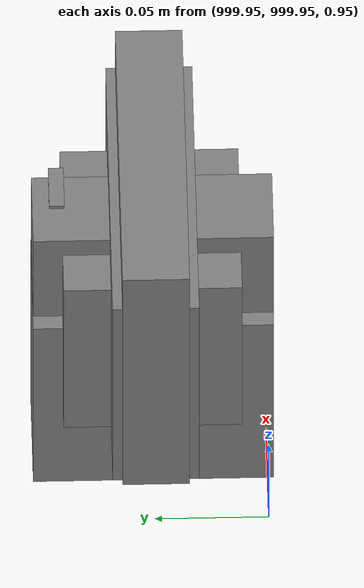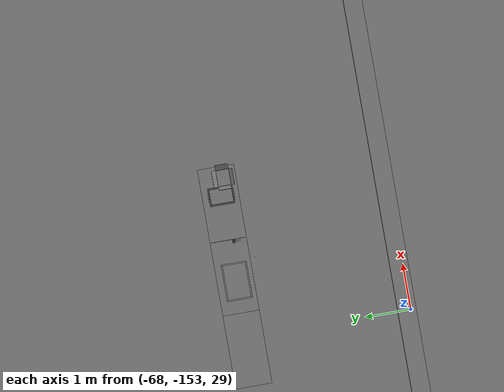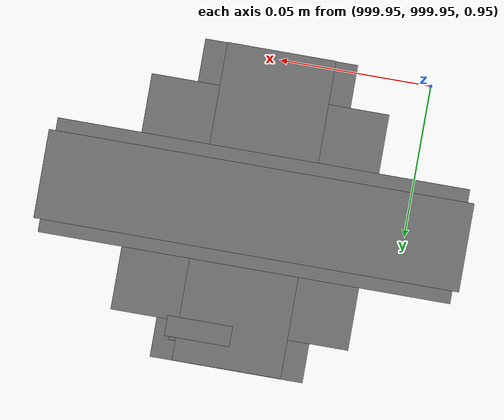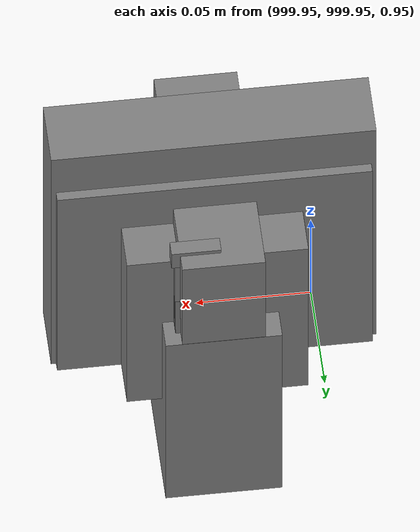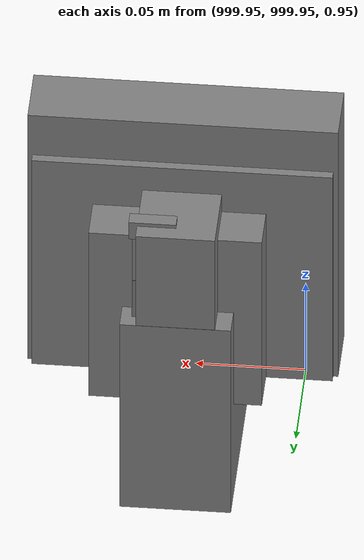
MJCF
<mujoco>
    <option gravity="0.000000000 0.000000000 -9.810000420" timestep="0.0049999999" integrator="implicitfast" density="1.225" viscosity="1.8000001e-05" noslip_iterations="10" iterations="100" sdf_iterations="50">
        <flag multiccd="disable"/>
    </option>
    <size memory="1000M"/>
    <compiler coordinate="local"/>
    <worldbody>
        <light cutoff="30" pos="0 1 1" dir="0 -1 -2"/>
        <light cutoff="30" pos="0 -1 1" dir="0 1 -2"/>
        <body pos="1000.000000000 1000.000000000 1.000000000" euler="0.000000000 0.000000000 180.000000000" name="openloong_gripper_2f85_fix_base_usda_cpu_fan">
            <geom contype="1" conaffinity="1" density="1000" type="box" material="" rgba="0.500000000 0.500000000 0.500000000 1.000000000" solimp="0.899999976 0.949999988 0.001000000" friction="1.000000000 0.005000000 0.000100000" solref="0.020000000 1.000000000" margin="0" condim="3" group="0" pos="0.000000000 0.000000000 0.070034981" quat="0.000000000 0.000000000 0.000000000 1.000000000" size="0.070700005 0.014699999 0.070700005" name="openloong_gripper_2f85_fix_base_usda_geom_B981320D_7349_416F_B02F_5821FC968776"/>
            <freejoint name="openloong_gripper_2f85_fix_base_usda_cpu_fan_joint"/>
            <site size="0.005000000 0.005000000 0.005000000" rgba="0.500000000 0.500000000 0.500000000 1.000000000" pos="0.000000000 0.000000000 0.000000000" quat="0.999961913 0.008726535 0.000000000 0.000000000" group="0" type="sphere" name="openloong_gripper_2f85_fix_base_usda_cpu_fancsite"/>
        </body>
        <body pos="1000.000000000 1000.000000000 1.000000000" euler="0.000000000 0.000000000 180.000000000" name="openloong_gripper_2f85_fix_base_usda_battery_01">
            <geom contype="1" conaffinity="1" density="1000" type="box" material="" rgba="0.500000000 0.500000000 0.500000000 1.000000000" solimp="0.899999976 0.949999988 0.001000000" friction="1.000000000 0.005000000 0.000100000" solref="0.020000000 1.000000000" margin="0" condim="3" group="0" pos="-0.011123657 -0.041940309 0.101691343" quat="1.000000000 0.000000000 0.000000000 0.000000000" size="0.010800000 0.003375000 0.004725000" name="openloong_gripper_2f85_fix_base_usda_geom_95C95858_C431_427D_9C1E_F80DAEB8FF35"/>
            <geom contype="1" conaffinity="1" density="1000" type="box" material="" rgba="0.500000000 0.500000000 0.500000000 1.000000000" solimp="0.899999976 0.949999988 0.001000000" friction="1.000000000 0.005000000 0.000100000" solref="0.020000000 1.000000000" margin="0" condim="3" group="0" pos="-0.010876465 -0.044247437 0.047066893" quat="0.998702705 -0.050920475 0.000000000 0.000000000" size="0.009450001 0.002700000 0.024975000" name="openloong_gripper_2f85_fix_base_usda_geom_79F76CAA_07AD_41DE_A444_6A70B254529E"/>
            <geom contype="1" conaffinity="1" density="1000" type="box" material="" rgba="0.500000000 0.500000000 0.500000000 1.000000000" solimp="0.899999976 0.949999988 0.001000000" friction="1.000000000 0.005000000 0.000100000" solref="0.020000000 1.000000000" margin="0" condim="3" group="0" pos="-0.001235962 -0.000659180 0.047381196" quat="1.000000000 0.000000000 0.000000000 0.000000000" size="0.039420001 0.039150000 0.047250003" name="openloong_gripper_2f85_fix_base_usda_geom_20D45054_0C0A_4341_AE81_BDC8EDF076CB"/>
            <geom contype="1" conaffinity="1" density="1000" type="box" material="" rgba="0.500000000 0.500000000 0.500000000 1.000000000" solimp="0.899999976 0.949999988 0.001000000" friction="1.000000000 0.005000000 0.000100000" solref="0.020000000 1.000000000" margin="0" condim="3" group="0" pos="-0.010876465 -0.039138794 0.009851727" quat="1.000000000 0.000000000 0.000000000 0.000000000" size="0.009450001 0.010800000 0.013500000" name="openloong_gripper_2f85_fix_base_usda_geom_4B5EFDDA_F333_430E_B2B7_6A1140F13DD9"/>
            <geom contype="1" conaffinity="1" density="1000" type="box" material="" rgba="0.500000000 0.500000000 0.500000000 1.000000000" solimp="0.899999976 0.949999988 0.001000000" friction="1.000000000 0.005000000 0.000100000" solref="0.020000000 1.000000000" margin="0" condim="3" group="0" pos="-0.010876465 -0.041528322 0.071508206" quat="1.000000000 0.000000000 0.000000000 0.000000000" size="0.009450001 0.002700000 0.027000001" name="openloong_gripper_2f85_fix_base_usda_geom_E116E24C_0437_45A0_98B8_A9740F0706E5"/>
            <freejoint name="openloong_gripper_2f85_fix_base_usda_battery_01_joint"/>
            <site size="0.005000000 0.005000000 0.005000000" rgba="0.500000000 0.500000000 0.500000000 1.000000000" pos="0.000000000 0.000000000 0.000000000" quat="0.999961913 0.008726500 0.000000000 0.000000000" group="0" type="sphere" name="openloong_gripper_2f85_fix_base_usda_battery_01site"/>
        </body>
        <body pos="1000.000000000 1000.000000000 1.000000000" euler="0.000000000 0.000000000 180.000000000" name="openloong_gripper_2f85_fix_base_usda_wifi_box">
            <geom contype="1" conaffinity="1" density="1000" type="box" material="" rgba="0.500000000 0.500000000 0.500000000 1.000000000" solimp="0.899999976 0.949999988 0.001000000" friction="1.000000000 0.005000000 0.000100000" solref="0.020000000 1.000000000" margin="0" condim="3" group="0" pos="0.000000000 0.000000000 0.058978677" quat="0.000000000 0.000000047 0.000000000 1.000000000" size="0.068499997 0.018999999 0.059000000" name="openloong_gripper_2f85_fix_base_usda_geom_C00CFDCF_317E_40BF_ACD6_4828AA9D833F"/>
            <freejoint name="openloong_gripper_2f85_fix_base_usda_wifi_box_joint"/>
            <site size="0.005000000 0.005000000 0.005000000" rgba="0.500000000 0.500000000 0.500000000 1.000000000" pos="0.000000000 0.000000000 0.000000000" quat="0.999961913 0.008726500 0.000000000 0.000000000" group="0" type="sphere" name="openloong_gripper_2f85_fix_base_usda_wifi_boxsite"/>
        </body>
        <body pos="-65.973861694 -149.765472412 31.169101715" euler="108.112068176 65.642242432 123.508636475" mocap="true" name="spotlight6_SpotLight"/>
        <body pos="1000.000000000 1000.000000000 1.000000000" euler="0.000011953 0.000005123 -179.999984741" name="openloong_gripper_2f85_fix_base_usda_intel_box">
            <geom contype="1" conaffinity="1" density="1000" type="box" material="" rgba="0.500000000 0.500000000 0.500000000 1.000000000" solimp="0.899999976 0.949999988 0.001000000" friction="1.000000000 0.005000000 0.000100000" solref="0.020000000 1.000000000" margin="0" condim="3" group="0" pos="0.000000000 -0.000067139 0.000082284" quat="0.707106709 0.000000225 0.000000253 0.707106650" size="0.052800003 0.025300000 0.052800003" name="openloong_gripper_2f85_fix_base_usda_geom_65244349_F894_4070_BD9C_3D3212BD4AB7"/>
            <freejoint name="openloong_gripper_2f85_fix_base_usda_intel_box_joint"/>
            <site size="0.005000000 0.005000000 0.005000000" rgba="0.500000000 0.500000000 0.500000000 1.000000000" pos="0.000000000 0.000000000 0.000000000" quat="0.999961913 0.008726500 0.000000000 0.000000000" group="0" type="sphere" name="openloong_gripper_2f85_fix_base_usda_intel_boxsite"/>
        </body>
        <body pos="1000.000000000 999.999938965 1.000000000" euler="0.000000000 0.000000000 180.000000000" name="openloong_gripper_2f85_fix_base_usda_intelcore_i5">
            <geom contype="1" conaffinity="1" density="1000" type="box" material="" rgba="0.500000000 0.500000000 0.500000000 1.000000000" solimp="0.899999976 0.949999988 0.001000000" friction="1.000000000 0.005000000 0.000100000" solref="0.020000000 1.000000000" margin="0" condim="3" group="0" pos="0.000000000 0.000000000 0.051722717" quat="0.707106709 0.000000000 0.000000000 -0.707106769" size="0.052800000 0.018080002 0.052800000" name="openloong_gripper_2f85_fix_base_usda_geom_BF81BC44_D9C0_4246_B55E_B4148D072946"/>
            <freejoint name="openloong_gripper_2f85_fix_base_usda_intelcore_i5_joint"/>
            <site size="0.005000000 0.005000000 0.005000000" rgba="0.500000000 0.500000000 0.500000000 1.000000000" pos="0.000000000 0.000000000 0.000000000" quat="0.999961913 0.008726534 0.000000000 0.000000000" group="0" type="sphere" name="openloong_gripper_2f85_fix_base_usda_intelcore_i5site"/>
        </body>
        <body pos="-65.817443848 -149.438430786 31.169645309" euler="-6.743350029 -65.272369385 133.242004395" mocap="true" name="spotlight1_SpotLight"/>
        <body pos="-65.814292908 -149.535079956 31.164106369" euler="-117.724998474 77.504409790 141.683654785" mocap="true" name="spotlight4_SpotLight"/>
        <body pos="-64.866622925 -149.383972168 30.183746338" euler="89.999984741 89.999946594 0.000000000" name="openloong_gripper_2f85_fix_base_usda_bluebox_01">
            <geom contype="1" conaffinity="1" density="1000" type="box" material="" rgba="0.500000000 0.500000000 0.500000000 1.000000000" solimp="0.899999976 0.949999988 0.001000000" friction="1.000000000 0.005000000 0.000100000" solref="0.020000000 1.000000000" margin="0" condim="3" group="0" pos="0.276580811 0.187225342 0.000068665" quat="0.707106948 0.000077471 0.707106352 0.000077486" size="0.100000001 0.057999998 0.010000000" name="openloong_gripper_2f85_fix_base_usda_geom_7CECBA11_6068_4D63_A787_679D4611C3C1"/>
            <geom contype="1" conaffinity="1" density="1000" type="box" material="" rgba="0.500000000 0.500000000 0.500000000 1.000000000" solimp="0.899999976 0.949999988 0.001000000" friction="1.000000000 0.005000000 0.000100000" solref="0.020000000 1.000000000" margin="0" condim="3" group="0" pos="0.000000000 0.002883911 0.000000000" quat="0.999999881 0.000000000 0.000000000 0.000000000" size="0.254000008 0.003000000 0.172000006" name="openloong_gripper_2f85_fix_base_usda_geom_ED7C35B2_0472_43BF_A9EC_050773ACDC1C"/>
            <geom contype="1" conaffinity="1" density="1000" type="box" material="" rgba="0.500000000 0.500000000 0.500000000 1.000000000" solimp="0.899999976 0.949999988 0.001000000" friction="1.000000000 0.005000000 0.000100000" solref="0.020000000 1.000000000" margin="0" condim="3" group="0" pos="0.000000000 0.124874115 0.173484802" quat="0.999796331 0.020176515 -0.000000015 0.000000030" size="0.259999990 0.119999997 0.007000000" name="openloong_gripper_2f85_fix_base_usda_geom_3022B906_6C79_46FB_9BB1_E672AAA8C818"/>
            <geom contype="1" conaffinity="1" density="1000" type="box" material="" rgba="0.500000000 0.500000000 0.500000000 1.000000000" solimp="0.899999976 0.949999988 0.001000000" friction="1.000000000 0.005000000 0.000100000" solref="0.020000000 1.000000000" margin="0" condim="3" group="0" pos="0.000000000 0.124874115 -0.173469543" quat="0.999796331 -0.020176545 -0.000000015 0.000000000" size="0.259999990 0.119999997 0.007000000" name="openloong_gripper_2f85_fix_base_usda_geom_9CDFD7EB_78B0_4AE9_A34C_B3EAAF872D27"/>
            <geom contype="1" conaffinity="1" density="1000" type="box" material="" rgba="0.500000000 0.500000000 0.500000000 1.000000000" solimp="0.899999976 0.949999988 0.001000000" friction="1.000000000 0.005000000 0.000100000" solref="0.020000000 1.000000000" margin="0" condim="3" group="0" pos="0.000000000 0.214008331 0.188980103" quat="0.999912977 0.013176724 0.000000015 0.000000000" size="0.259999990 0.029999999 0.012500000" name="openloong_gripper_2f85_fix_base_usda_geom_D9C2A7CA_DE0D_4A6D_9B41_9B536B8B1B11"/>
            <geom contype="1" conaffinity="1" density="1000" type="box" material="" rgba="0.500000000 0.500000000 0.500000000 1.000000000" solimp="0.899999976 0.949999988 0.001000000" friction="1.000000000 0.005000000 0.000100000" solref="0.020000000 1.000000000" margin="0" condim="3" group="0" pos="-0.258361816 0.125289917 0.001876831" quat="0.702796936 -0.020792112 0.710783124 0.020769298" size="0.189999998 0.119999997 0.009000000" name="openloong_gripper_2f85_fix_base_usda_geom_C46C13F0_42E5_42B0_84B7_98A45815218C"/>
            <geom contype="1" conaffinity="1" density="1000" type="box" material="" rgba="0.500000000 0.500000000 0.500000000 1.000000000" solimp="0.899999976 0.949999988 0.001000000" friction="1.000000000 0.005000000 0.000100000" solref="0.020000000 1.000000000" margin="0" condim="3" group="0" pos="0.000000000 0.214008331 -0.188980103" quat="0.999912977 -0.013176769 0.000000030 0.000000015" size="0.259999990 0.029999999 0.012500000" name="openloong_gripper_2f85_fix_base_usda_geom_81D6D3C4_4B62_4FE4_B1B1_250BCE739446"/>
            <geom contype="1" conaffinity="1" density="1000" type="box" material="" rgba="0.500000000 0.500000000 0.500000000 1.000000000" solimp="0.899999976 0.949999988 0.001000000" friction="1.000000000 0.005000000 0.000100000" solref="0.020000000 1.000000000" margin="0" condim="3" group="0" pos="-0.276611328 0.187225342 0.000068665" quat="0.707106650 0.000077441 0.707106709 0.000077456" size="0.100000001 0.057999998 0.010000000" name="openloong_gripper_2f85_fix_base_usda_geom_C41EA92C_40F3_4105_AFA1_8951455E3DD9"/>
            <geom contype="1" conaffinity="1" density="1000" type="box" material="" rgba="0.500000000 0.500000000 0.500000000 1.000000000" solimp="0.899999976 0.949999988 0.001000000" friction="1.000000000 0.005000000 0.000100000" solref="0.020000000 1.000000000" margin="0" condim="3" group="0" pos="0.258331299 0.125289917 0.001876831" quat="0.702851415 0.018856421 0.710823774 -0.019329369" size="0.189999998 0.119999997 0.009000000" name="openloong_gripper_2f85_fix_base_usda_geom_4C64D96A_FF3B_4E56_8CCC_DBFE9DF1EA60"/>
            <freejoint name="openloong_gripper_2f85_fix_base_usda_bluebox_01_joint"/>
            <site size="0.005000000 0.005000000 0.005000000" rgba="0.500000000 0.500000000 0.500000000 1.000000000" pos="0.000000000 0.000000000 0.000000000" quat="0.999961913 0.008726534 0.000000000 0.000000000" group="0" type="sphere" name="openloong_gripper_2f85_fix_base_usda_bluebox_01site"/>
        </body>
        <body pos="-64.496299744 -149.491867065 30.235729218" euler="0.000000000 0.000000000 89.999946594" name="openloong_gripper_2f85_fix_base_usda_cardboardbox_01">
            <geom contype="1" conaffinity="1" density="1000" type="box" material="" rgba="0.500000000 0.500000000 0.500000000 1.000000000" solimp="0.899999976 0.949999988 0.001000000" friction="1.000000000 0.005000000 0.000100000" solref="0.020000000 1.000000000" margin="0" condim="3" group="0" pos="-0.003166199 -0.004086494 0.005052090" quat="1.000000000 0.000000000 0.000000000 0.000000000" size="0.142499998 0.177500010 0.005000000" name="openloong_gripper_2f85_fix_base_usda_geom_AC6799F2_37FD_4CD7_8C99_63A32DD9FD6E"/>
            <geom contype="1" conaffinity="1" density="1000" type="box" material="" rgba="0.500000000 0.500000000 0.500000000 1.000000000" solimp="0.899999976 0.949999988 0.001000000" friction="1.000000000 0.005000000 0.000100000" solref="0.020000000 1.000000000" margin="0" condim="3" group="0" pos="-0.003166199 0.170316696 0.150570869" quat="1.000000000 0.000000000 0.000000000 0.000000000" size="0.142499998 0.005000000 0.149999991" name="openloong_gripper_2f85_fix_base_usda_geom_3C593461_E8C5_444C_8244_2CF3F3045CA3"/>
            <geom contype="1" conaffinity="1" density="1000" type="box" material="" rgba="0.500000000 0.500000000 0.500000000 1.000000000" solimp="0.899999976 0.949999988 0.001000000" friction="1.000000000 0.005000000 0.000100000" solref="0.020000000 1.000000000" margin="0" condim="3" group="0" pos="-0.147399902 -0.005307198 0.150570869" quat="1.000000000 0.000000000 0.000000000 0.000000000" size="0.005000000 0.177500010 0.149999991" name="openloong_gripper_2f85_fix_base_usda_geom_F742AA20_1207_4B5F_A669_5ED42D7C5A1F"/>
            <geom contype="1" conaffinity="1" density="1000" type="box" material="" rgba="0.500000000 0.500000000 0.500000000 1.000000000" solimp="0.899999976 0.949999988 0.001000000" friction="1.000000000 0.005000000 0.000100000" solref="0.020000000 1.000000000" margin="0" condim="3" group="0" pos="0.140275955 -0.005307198 0.150570869" quat="1.000000000 0.000000000 0.000000000 0.000000000" size="0.005000000 0.177500010 0.149999991" name="openloong_gripper_2f85_fix_base_usda_geom_6BFB41BF_F8C0_4A3C_8E96_659BE719A891"/>
            <geom contype="1" conaffinity="1" density="1000" type="box" material="" rgba="0.500000000 0.500000000 0.500000000 1.000000000" solimp="0.899999976 0.949999988 0.001000000" friction="1.000000000 0.005000000 0.000100000" solref="0.020000000 1.000000000" margin="0" condim="3" group="0" pos="-0.003166199 -0.181550980 0.150570869" quat="1.000000000 0.000000000 0.000000000 0.000000000" size="0.142499998 0.005000000 0.149999991" name="openloong_gripper_2f85_fix_base_usda_geom_D9EB511B_5D61_4237_A6D8_8837153384C8"/>
            <freejoint name="openloong_gripper_2f85_fix_base_usda_cardboardbox_01_joint"/>
            <site size="0.005000000 0.005000000 0.005000000" rgba="0.500000000 0.500000000 0.500000000 1.000000000" pos="0.000000000 0.000000000 0.000000000" quat="0.999961913 0.008726535 0.000000000 0.000000000" group="0" type="sphere" name="openloong_gripper_2f85_fix_base_usda_site_58295299_1163_4D77_B1E5_855980890D44"/>
            <body pos="0.139160156 -0.004048347 0.301930904" euler="-179.999954224 49.383502960 179.999954224" name="openloong_gripper_2f85_fix_base_usda_A1_006">
                <geom contype="1" conaffinity="1" density="1000" type="box" material="" rgba="0.500000000 0.500000000 0.500000000 1.000000000" solimp="0.899999976 0.949999988 0.001000000" friction="1.000000000 0.005000000 0.000100000" solref="0.020000000 1.000000000" margin="0" condim="3" group="0" pos="-0.071587563 0.000009537 0.001745224" quat="0.999999881 0.000000000 0.000000000 0.000000000" size="0.071249999 0.179999992 0.002500000" name="openloong_gripper_2f85_fix_base_usda_geom_739DB3DF_DD06_4DD3_8BB3_05A8EE8F96BE"/>
                <joint armature="0" stiffness="0.07" damping="0.0099999998" axis="0.000000 1.000000 0.000000" type="hinge" name="openloong_gripper_2f85_fix_base_usda_A1_006"/>
            </body>
            <body pos="-0.145902634 -0.004086494 0.301938057" euler="-180.000000000 -60.000011444 -180.000000000" name="openloong_gripper_2f85_fix_base_usda_A2_006">
                <geom contype="1" conaffinity="1" density="1000" type="box" material="" rgba="0.500000000 0.500000000 0.500000000 1.000000000" solimp="0.899999976 0.949999988 0.001000000" friction="1.000000000 0.005000000 0.000100000" solref="0.020000000 1.000000000" margin="0" condim="3" group="0" pos="0.071268082 0.000009537 0.002717972" quat="0.000002921 0.000000000 -0.000000030 0.999999881" size="0.071249999 0.179999992 0.002500000" name="openloong_gripper_2f85_fix_base_usda_geom_E7FCC6F6_2994_4904_BD06_4B438A96C044"/>
                <joint armature="0" stiffness="0.07" damping="0.0099999998" axis="0.000000 1.000000 0.000000" type="hinge" name="openloong_gripper_2f85_fix_base_usda_A2_006"/>
            </body>
            <body pos="-0.003385544 0.175991058 0.301930904" euler="-125.858116150 -0.000004561 0.000002331" name="openloong_gripper_2f85_fix_base_usda_B2_006">
                <geom contype="1" conaffinity="1" density="1000" type="box" material="" rgba="0.500000000 0.500000000 0.500000000 1.000000000" solimp="0.899999976 0.949999988 0.001000000" friction="1.000000000 0.005000000 0.000100000" solref="0.020000000 1.000000000" margin="0" condim="3" group="0" pos="0.000009537 -0.070939064 -0.002470016" quat="0.999614120 0.027776197 -0.000000015 0.000000030" size="0.137500003 0.064999998 0.005000000" name="openloong_gripper_2f85_fix_base_usda_geom_4D8B87DD_94C6_4173_933F_26CC21D34BC2"/>
                <joint armature="0" stiffness="0.07" damping="0.0099999998" axis="1.000000 0.000000 0.000000" type="hinge" name="openloong_gripper_2f85_fix_base_usda_B2_006"/>
            </body>
            <body pos="-0.003385544 -0.184140205 0.301938057" euler="147.805557251 0.000000000 0.000000000" name="openloong_gripper_2f85_fix_base_usda_B1_006">
                <geom contype="1" conaffinity="1" density="1000" type="box" material="" rgba="0.500000000 0.500000000 0.500000000 1.000000000" solimp="0.899999976 0.949999988 0.001000000" friction="1.000000000 0.005000000 0.000100000" solref="0.020000000 1.000000000" margin="0" condim="3" group="0" pos="-0.000028610 0.070202351 -0.002703667" quat="0.999614179 -0.027776167 0.000000000 0.000000000" size="0.137500003 0.064999998 0.005000000" name="openloong_gripper_2f85_fix_base_usda_geom_B7FBF27A_91F7_4252_B06E_9FD510593284"/>
                <joint armature="0" stiffness="0.07" damping="0.0099999998" axis="1.000000 0.000000 0.000000" type="hinge" name="openloong_gripper_2f85_fix_base_usda_B1_006"/>
            </body>
        </body>
        <body pos="-65.882858276 -149.481979370 30.229999542" euler="-64.487716675 0.000000000 0.000000000" name="openloong_gripper_2f85_fix_base_usda_Barcode">
            <geom contype="1" conaffinity="1" density="1000" type="box" material="" rgba="0.500000000 0.500000000 0.500000000 1.000000000" solimp="0.899999976 0.949999988 0.001000000" friction="1.000000000 0.005000000 0.000100000" solref="0.020000000 1.000000000" margin="0" condim="3" group="0" pos="0.000000000 0.013038635 0.001419067" quat="0.000000000 0.000000000 0.000000000 1.000000119" size="0.034000002 0.010000000 0.017999999" name="openloong_gripper_2f85_fix_base_usda_geom_AFA9F6AE_73F6_4A51_9351_7E3EB8FD8CBA"/>
            <geom contype="1" conaffinity="1" density="1000" type="box" material="" rgba="0.500000000 0.500000000 0.500000000 1.000000000" solimp="0.899999976 0.949999988 0.001000000" friction="1.000000000 0.005000000 0.000100000" solref="0.020000000 1.000000000" margin="0" condim="3" group="0" pos="0.000000000 -0.035301208 -0.007095337" quat="0.000000000 0.000000000 -0.043619365 0.999048233" size="0.028999999 0.010000000 0.020000000" name="openloong_gripper_2f85_fix_base_usda_geom_CCE12B92_100E_44AD_B441_2BFD2009675B"/>
            <geom contype="1" conaffinity="1" density="1000" type="box" material="" rgba="0.500000000 0.500000000 0.500000000 1.000000000" solimp="0.899999976 0.949999988 0.001000000" friction="1.000000000 0.005000000 0.000100000" solref="0.020000000 1.000000000" margin="0" condim="3" group="0" pos="0.000000000 -0.043411255 -0.011749268" quat="0.922262907 0.386563420 0.000000000 0.000000000" size="0.026000001 0.010000000 0.020000000" name="openloong_gripper_2f85_fix_base_usda_geom_5B488B25_CFF2_4A0E_B603_33539BC699C8"/>
            <geom contype="1" conaffinity="1" density="1000" type="box" material="" rgba="0.500000000 0.500000000 0.500000000 1.000000000" solimp="0.899999976 0.949999988 0.001000000" friction="1.000000000 0.005000000 0.000100000" solref="0.020000000 1.000000000" margin="0" condim="3" group="0" pos="0.000000000 -0.016967773 -0.031860352" quat="0.000000000 0.000000000 0.000000000 1.000000119" size="0.008000000 0.010000000 0.013000000" name="openloong_gripper_2f85_fix_base_usda_geom_E3FA99D2_1FBB_4F5B_B6E6_F6CBB8EA2D47"/>
            <geom contype="1" conaffinity="1" density="1000" type="box" material="" rgba="0.500000000 0.500000000 0.500000000 1.000000000" solimp="0.899999976 0.949999988 0.001000000" friction="1.000000000 0.005000000 0.000100000" solref="0.020000000 1.000000000" margin="0" condim="3" group="0" pos="0.000000000 -0.001869202 0.000312805" quat="0.953716993 0.300705761 0.000000000 0.000000000" size="0.032000002 0.010000000 0.018999999" name="openloong_gripper_2f85_fix_base_usda_geom_40A895F3_DF55_47AB_A7E6_07E3ADA7E618"/>
            <geom contype="1" conaffinity="1" density="1000" type="box" material="" rgba="0.500000000 0.500000000 0.500000000 1.000000000" solimp="0.899999976 0.949999988 0.001000000" friction="1.000000000 0.005000000 0.000100000" solref="0.020000000 1.000000000" margin="0" condim="3" group="0" pos="0.000000000 -0.019531250 -0.003173828" quat="0.953716993 0.300705761 0.000000000 0.000000000" size="0.030999999 0.010000000 0.020000000" name="openloong_gripper_2f85_fix_base_usda_geom_08805678_06FB_4046_982C_0B654613F89A"/>
            <geom contype="1" conaffinity="1" density="1000" type="box" material="" rgba="0.500000000 0.500000000 0.500000000 1.000000000" solimp="0.899999976 0.949999988 0.001000000" friction="1.000000000 0.005000000 0.000100000" solref="0.020000000 1.000000000" margin="0" condim="3" group="0" pos="0.000000000 -0.035301208 -0.007095337" quat="0.953716993 0.300705761 0.000000000 0.000000000" size="0.028999999 0.010000000 0.020000000" name="openloong_gripper_2f85_fix_base_usda_geom_1CECAB60_87C4_4CD8_B01D_659202FCD669"/>
            <geom contype="1" conaffinity="1" density="1000" type="box" material="" rgba="0.500000000 0.500000000 0.500000000 1.000000000" solimp="0.899999976 0.949999988 0.001000000" friction="1.000000000 0.005000000 0.000100000" solref="0.020000000 1.000000000" margin="0" condim="3" group="0" pos="0.000000000 -0.042617798 -0.071121216" quat="0.000000000 0.000000000 0.000000000 1.000000119" size="0.013000000 0.021000000 0.059999999" name="openloong_gripper_2f85_fix_base_usda_geom_47419135_35DA_473A_A784_AF2A902E0759"/>
            <freejoint name="openloong_gripper_2f85_fix_base_usda_Barcode_joint"/>
            <site size="0.005000000 0.005000000 0.005000000" rgba="0.500000000 0.500000000 0.500000000 1.000000000" pos="0.000000000 0.000000000 0.000000000" quat="1.000000000 0.000000000 0.000000000 0.000000000" group="0" type="sphere" name="openloong_gripper_2f85_fix_base_usda_Barcode_site"/>
        </body>
        <body pos="-66.745018005 -149.392349243 30.184000015" euler="0.000000000 0.000000000 89.999946594" name="[22333440329625]_Basket_01">
            <geom contype="1" conaffinity="1" density="1000" type="box" material="" rgba="0.500000000 0.500000000 0.500000000 1.000000000" solimp="0.899999976 0.949999988 0.001000000" friction="1.000000000 0.005000000 0.000100000" solref="0.020000000 1.000000000" margin="0" condim="3" group="0" pos="-0.052425385 0.389207840 0.089787483" quat="0.707107008 0.000000000 0.000000000 0.707106411" size="0.014249999 0.014249999 0.059999999" name="[22333440329625]_geom_C4A9FE09_71A5_405E_B66A_FAA3F01B512E"/>
            <geom contype="1" conaffinity="1" density="1000" type="box" material="" rgba="0.500000000 0.500000000 0.500000000 1.000000000" solimp="0.899999976 0.949999988 0.001000000" friction="1.000000000 0.005000000 0.000100000" solref="0.020000000 1.000000000" margin="0" condim="3" group="0" pos="0.264015198 -0.133043289 0.089787483" quat="0.707107008 0.000000000 0.000000000 0.707106411" size="0.014249999 0.014249999 0.059999999" name="[22333440329625]_geom_47F2E83B_093C_4AB0_9975_6589D4F1012F"/>
            <geom contype="1" conaffinity="1" density="1000" type="box" material="" rgba="0.500000000 0.500000000 0.500000000 1.000000000" solimp="0.899999976 0.949999988 0.001000000" friction="1.000000000 0.005000000 0.000100000" solref="0.020000000 1.000000000" margin="0" condim="3" group="0" pos="-0.264015198 -0.265548706 0.089793205" quat="0.707107008 0.000000000 0.000000000 0.707106411" size="0.014249999 0.014249999 0.059999999" name="[22333440329625]_geom_00DC592C_E518_4012_BBD5_808B20530283"/>
            <geom contype="1" conaffinity="1" density="1000" type="box" material="" rgba="0.500000000 0.500000000 0.500000000 1.000000000" solimp="0.899999976 0.949999988 0.001000000" friction="1.000000000 0.005000000 0.000100000" solref="0.020000000 1.000000000" margin="0" condim="3" group="0" pos="-0.160263062 -0.389322281 0.089793205" quat="0.707107008 0.000000000 0.000000000 0.707106411" size="0.014249999 0.014249999 0.059999999" name="[22333440329625]_geom_20C23B11_7419_42BD_8724_4E7FCF6AA6EE"/>
            <geom contype="1" conaffinity="1" density="1000" type="box" material="" rgba="0.500000000 0.500000000 0.500000000 1.000000000" solimp="0.899999976 0.949999988 0.001000000" friction="1.000000000 0.005000000 0.000100000" solref="0.020000000 1.000000000" margin="0" condim="3" group="0" pos="0.162265778 -0.389322281 0.089787483" quat="0.707107008 0.000000000 0.000000000 0.707106411" size="0.014249999 0.014249999 0.059999999" name="[22333440329625]_geom_F1DBA3F8_CC85_4F11_A079_77FA2E3256EC"/>
            <geom contype="1" conaffinity="1" density="1000" type="box" material="" rgba="0.500000000 0.500000000 0.500000000 1.000000000" solimp="0.899999976 0.949999988 0.001000000" friction="1.000000000 0.005000000 0.000100000" solref="0.020000000 1.000000000" margin="0" condim="3" group="0" pos="0.264015198 0.389207840 0.089787483" quat="0.707107008 0.000000000 0.000000000 0.707106411" size="0.014249999 0.014249999 0.059999999" name="[22333440329625]_geom_BA5DC605_6924_4AED_B34A_97C9D9AF05D2"/>
            <geom contype="1" conaffinity="1" density="1000" type="box" material="" rgba="0.500000000 0.500000000 0.500000000 1.000000000" solimp="0.899999976 0.949999988 0.001000000" friction="1.000000000 0.005000000 0.000100000" solref="0.020000000 1.000000000" margin="0" condim="3" group="0" pos="-0.264015198 -0.133043289 0.089793205" quat="0.707107008 0.000000000 0.000000000 0.707106411" size="0.014249999 0.014249999 0.059999999" name="[22333440329625]_geom_9D49B03F_7171_40B3_8632_A18939D8F223"/>
            <geom contype="1" conaffinity="1" density="1000" type="box" material="" rgba="0.500000000 0.500000000 0.500000000 1.000000000" solimp="0.899999976 0.949999988 0.001000000" friction="1.000000000 0.005000000 0.000100000" solref="0.020000000 1.000000000" margin="0" condim="3" group="0" pos="-0.264026642 0.269256592 0.089793205" quat="0.707107008 0.000000000 0.000000000 0.707106411" size="0.014249999 0.014249999 0.059999999" name="[22333440329625]_geom_C526B5E4_29FB_4D3D_9A59_6D60FD291B11"/>
            <geom contype="1" conaffinity="1" density="1000" type="box" material="" rgba="0.500000000 0.500000000 0.500000000 1.000000000" solimp="0.899999976 0.949999988 0.001000000" friction="1.000000000 0.005000000 0.000100000" solref="0.020000000 1.000000000" margin="0" condim="3" group="0" pos="0.054462433 0.389207840 0.089787483" quat="0.707107008 0.000000000 0.000000000 0.707106411" size="0.014249999 0.014249999 0.059999999" name="[22333440329625]_geom_68D38274_1476_4CA9_B9C2_E880ABA8EC5C"/>
            <geom contype="1" conaffinity="1" density="1000" type="box" material="" rgba="0.500000000 0.500000000 0.500000000 1.000000000" solimp="0.899999976 0.949999988 0.001000000" friction="1.000000000 0.005000000 0.000100000" solref="0.020000000 1.000000000" margin="0" condim="3" group="0" pos="0.054462433 -0.389322281 0.089787483" quat="0.707107008 0.000000000 0.000000000 0.707106411" size="0.014249999 0.014249999 0.059999999" name="[22333440329625]_geom_7A716633_E008_47AB_8C44_1C970B23D7DA"/>
            <geom contype="1" conaffinity="1" density="1000" type="box" material="" rgba="0.500000000 0.500000000 0.500000000 1.000000000" solimp="0.899999976 0.949999988 0.001000000" friction="1.000000000 0.005000000 0.000100000" solref="0.020000000 1.000000000" margin="0" condim="3" group="0" pos="0.264015198 0.269256592 0.089793205" quat="0.707107008 0.000000000 0.000000000 0.707106411" size="0.014249999 0.014249999 0.059999999" name="[22333440329625]_geom_14872EF7_2608_440F_A8D7_89B1BD58EC3C"/>
            <geom contype="1" conaffinity="1" density="1000" type="box" material="" rgba="0.500000000 0.500000000 0.500000000 1.000000000" solimp="0.899999976 0.949999988 0.001000000" friction="1.000000000 0.005000000 0.000100000" solref="0.020000000 1.000000000" margin="0" condim="3" group="0" pos="0.264015198 -0.389322281 0.089787483" quat="0.707107008 0.000000000 0.000000000 0.707106411" size="0.014249999 0.014249999 0.059999999" name="[22333440329625]_geom_163A3056_C11A_4B7F_A81D_495B3BC0FF63"/>
            <geom contype="1" conaffinity="1" density="1000" type="box" material="" rgba="0.500000000 0.500000000 0.500000000 1.000000000" solimp="0.899999976 0.949999988 0.001000000" friction="1.000000000 0.005000000 0.000100000" solref="0.020000000 1.000000000" margin="0" condim="3" group="0" pos="0.000000000 0.000000000 0.015998840" quat="0.707107008 0.000000000 0.000000000 0.707106411" size="0.403499991 0.279000014 0.015750000" name="[22333440329625]_geom_A315058F_C858_48C7_AAE0_18F529618EEB"/>
            <geom contype="1" conaffinity="1" density="1000" type="box" material="" rgba="0.500000000 0.500000000 0.500000000 1.000000000" solimp="0.899999976 0.949999988 0.001000000" friction="1.000000000 0.005000000 0.000100000" solref="0.020000000 1.000000000" margin="0" condim="3" group="0" pos="0.000000000 -0.389476776 0.163619041" quat="0.707107008 0.000000000 0.000000000 0.707106411" size="0.015000000 0.277500004 0.015750000" name="[22333440329625]_geom_807EFBE6_EF2D_44AE_8A48_16C93D577AE7"/>
            <geom contype="1" conaffinity="1" density="1000" type="box" material="" rgba="0.500000000 0.500000000 0.500000000 1.000000000" solimp="0.899999976 0.949999988 0.001000000" friction="1.000000000 0.005000000 0.000100000" solref="0.020000000 1.000000000" margin="0" condim="3" group="0" pos="0.162265778 0.389207840 0.089787483" quat="0.707107008 0.000000000 0.000000000 0.707106411" size="0.014249999 0.014249999 0.059999999" name="[22333440329625]_geom_D704F0F1_BFF1_410C_933F_8FCF8547CC24"/>
            <geom contype="1" conaffinity="1" density="1000" type="box" material="" rgba="0.500000000 0.500000000 0.500000000 1.000000000" solimp="0.899999976 0.949999988 0.001000000" friction="1.000000000 0.005000000 0.000100000" solref="0.020000000 1.000000000" margin="0" condim="3" group="0" pos="0.000000000 0.389471054 0.163619041" quat="0.707107008 0.000000000 0.000000000 0.707106411" size="0.015000000 0.277500004 0.015750000" name="[22333440329625]_geom_E18002FD_35E1_448E_999B_2D6B9FD464E1"/>
            <geom contype="1" conaffinity="1" density="1000" type="box" material="" rgba="0.500000000 0.500000000 0.500000000 1.000000000" solimp="0.899999976 0.949999988 0.001000000" friction="1.000000000 0.005000000 0.000100000" solref="0.020000000 1.000000000" margin="0" condim="3" group="0" pos="-0.263511658 0.000000000 0.163619041" quat="0.707107008 0.000000000 0.000000000 0.707106411" size="0.403499991 0.015000000 0.015750000" name="[22333440329625]_geom_7F517D4E_E047_46AC_8EB1_BF3A2D779B03"/>
            <geom contype="1" conaffinity="1" density="1000" type="box" material="" rgba="0.500000000 0.500000000 0.500000000 1.000000000" solimp="0.899999976 0.949999988 0.001000000" friction="1.000000000 0.005000000 0.000100000" solref="0.020000000 1.000000000" margin="0" condim="3" group="0" pos="-0.264015198 0.141334534 0.089793205" quat="0.707107008 0.000000000 0.000000000 0.707106411" size="0.014249999 0.014249999 0.059999999" name="[22333440329625]_geom_282E04BE_3FF2_450A_834C_5250240B81C2"/>
            <geom contype="1" conaffinity="1" density="1000" type="box" material="" rgba="0.500000000 0.500000000 0.500000000 1.000000000" solimp="0.899999976 0.949999988 0.001000000" friction="1.000000000 0.005000000 0.000100000" solref="0.020000000 1.000000000" margin="0" condim="3" group="0" pos="0.264015198 -0.265548706 0.089787483" quat="0.707107008 0.000000000 0.000000000 0.707106411" size="0.014249999 0.014249999 0.059999999" name="[22333440329625]_geom_A7EDE8BA_9402_429F_B076_FF4D82139802"/>
            <geom contype="1" conaffinity="1" density="1000" type="box" material="" rgba="0.500000000 0.500000000 0.500000000 1.000000000" solimp="0.899999976 0.949999988 0.001000000" friction="1.000000000 0.005000000 0.000100000" solref="0.020000000 1.000000000" margin="0" condim="3" group="0" pos="-0.160263062 0.389207840 0.089787483" quat="0.707107008 0.000000000 0.000000000 0.707106411" size="0.014249999 0.014249999 0.059999999" name="[22333440329625]_geom_2CA67306_536D_4D74_8DC0_8D55F9A44384"/>
            <geom contype="1" conaffinity="1" density="1000" type="box" material="" rgba="0.500000000 0.500000000 0.500000000 1.000000000" solimp="0.899999976 0.949999988 0.001000000" friction="1.000000000 0.005000000 0.000100000" solref="0.020000000 1.000000000" margin="0" condim="3" group="0" pos="-0.052425385 -0.389322281 0.089787483" quat="0.707107008 0.000000000 0.000000000 0.707106411" size="0.014249999 0.014249999 0.059999999" name="[22333440329625]_geom_35E9BD09_DC26_4821_A94F_2CEDD1EC212B"/>
            <geom contype="1" conaffinity="1" density="1000" type="box" material="" rgba="0.500000000 0.500000000 0.500000000 1.000000000" solimp="0.899999976 0.949999988 0.001000000" friction="1.000000000 0.005000000 0.000100000" solref="0.020000000 1.000000000" margin="0" condim="3" group="0" pos="-0.264026642 -0.389322281 0.089793205" quat="0.707107008 0.000000000 0.000000000 0.707106411" size="0.014249999 0.014249999 0.059999999" name="[22333440329625]_geom_86C18D22_306B_4F95_A717_FC0F8F7A2A17"/>
            <geom contype="1" conaffinity="1" density="1000" type="box" material="" rgba="0.500000000 0.500000000 0.500000000 1.000000000" solimp="0.899999976 0.949999988 0.001000000" friction="1.000000000 0.005000000 0.000100000" solref="0.020000000 1.000000000" margin="0" condim="3" group="0" pos="0.264015198 0.141334534 0.089787483" quat="0.707107008 0.000000000 0.000000000 0.707106411" size="0.014249999 0.014249999 0.059999999" name="[22333440329625]_geom_BEF37268_1EFC_4D85_9B28_CD7F730311C5"/>
            <geom contype="1" conaffinity="1" density="1000" type="box" material="" rgba="0.500000000 0.500000000 0.500000000 1.000000000" solimp="0.899999976 0.949999988 0.001000000" friction="1.000000000 0.005000000 0.000100000" solref="0.020000000 1.000000000" margin="0" condim="3" group="0" pos="-0.264015198 0.389207840 0.089793205" quat="0.707107008 0.000000000 0.000000000 0.707106411" size="0.014249999 0.014249999 0.059999999" name="[22333440329625]_geom_30502C17_35F1_4D7B_AE9E_447BC59F7123"/>
            <geom contype="1" conaffinity="1" density="1000" type="box" material="" rgba="0.500000000 0.500000000 0.500000000 1.000000000" solimp="0.899999976 0.949999988 0.001000000" friction="1.000000000 0.005000000 0.000100000" solref="0.020000000 1.000000000" margin="0" condim="3" group="0" pos="0.264015198 0.004480362 0.089787483" quat="0.707107008 0.000000000 0.000000000 0.707106411" size="0.014249999 0.014249999 0.059999999" name="[22333440329625]_geom_7EEC0B80_1660_452E_ACB9_F928A7CEF2DE"/>
            <geom contype="1" conaffinity="1" density="1000" type="box" material="" rgba="0.500000000 0.500000000 0.500000000 1.000000000" solimp="0.899999976 0.949999988 0.001000000" friction="1.000000000 0.005000000 0.000100000" solref="0.020000000 1.000000000" margin="0" condim="3" group="0" pos="0.263694763 -0.000011444 0.163619041" quat="0.707107008 0.000000000 0.000000000 0.707106411" size="0.403499991 0.015000000 0.015750000" name="[22333440329625]_geom_C17C31D9_F3C0_4C88_8C4E_D225D16EA7A3"/>
            <geom contype="1" conaffinity="1" density="1000" type="box" material="" rgba="0.500000000 0.500000000 0.500000000 1.000000000" solimp="0.899999976 0.949999988 0.001000000" friction="1.000000000 0.005000000 0.000100000" solref="0.020000000 1.000000000" margin="0" condim="3" group="0" pos="-0.264015198 0.004480362 0.089793205" quat="0.707107008 0.000000000 0.000000000 0.707106411" size="0.014249999 0.014249999 0.059999999" name="[22333440329625]_geom_3256FE54_6551_462B_ABF9_CC4D547CFA9D"/>
            <freejoint name="[22333440329625]_joint_5E7F7D91_0BC5_4BB3_A1CE_94DAF47CF55E"/>
        </body>
        <body pos="0.000000000 0.000000000 0.000000000" euler="0.000000000 0.000000000 0.000000000" name="Static Objects_Static Objects">
            <geom contype="1" conaffinity="1" density="1000" type="box" material="" rgba="0.500000000 0.500000000 0.500000000 1.000000000" solimp="0.899999976 0.949999988 0.001000000" friction="1.000000000 0.005000000 0.000100000" solref="0.020000000 1.000000000" margin="0" condim="3" group="0" pos="-67.544113159 -149.365814209 29.727830887" quat="0.500000417 0.499999970 0.499999553 0.499999970" size="0.381000012 0.319999993 0.041000001" name="Static Objects_geom_01F06DE4_8AC5_4B17_BA2A_08005C5DE79C"/>
            <geom contype="1" conaffinity="1" density="1000" type="box" material="" rgba="0.500000000 0.500000000 0.500000000 1.000000000" solimp="0.899999976 0.949999988 0.001000000" friction="1.000000000 0.005000000 0.000100000" solref="0.020000000 1.000000000" margin="0" condim="3" group="0" pos="-68.239501953 -149.365814209 30.086868286" quat="0.500000417 0.499999970 0.499999553 0.499999970" size="0.370999992 0.039500002 0.745000005" name="Static Objects_geom_F0A7031F_9614_4752_9C7F_ECE6F8654BDA"/>
            <geom contype="1" conaffinity="1" density="1000" type="box" material="" rgba="0.500000000 0.500000000 0.500000000 1.000000000" solimp="0.899999976 0.949999988 0.001000000" friction="1.000000000 0.005000000 0.000100000" solref="0.020000000 1.000000000" margin="0" condim="3" group="0" pos="-68.239501953 -149.365814209 30.147235870" quat="0.500000417 0.499999970 0.499999553 0.499999970" size="0.400000006 0.022000000 0.800000012" name="Static Objects_geom_8FC17E41_2CFE_4BAE_9986_820F2E9FC975"/>
            <geom contype="1" conaffinity="1" density="1000" type="box" material="" rgba="0.500000000 0.500000000 0.500000000 1.000000000" solimp="0.899999976 0.949999988 0.001000000" friction="1.000000000 0.005000000 0.000100000" solref="0.020000000 1.000000000" margin="0" condim="3" group="0" pos="-68.934890747 -149.365814209 29.727830887" quat="0.500000417 0.499999970 0.499999553 0.499999970" size="0.381000012 0.319999993 0.041000001" name="Static Objects_geom_4E5DABFA_CF30_47E4_9569_2AAECFFB3D9D"/>
            <geom contype="1" conaffinity="1" density="1000" type="box" material="" rgba="0.500000000 0.500000000 0.500000000 1.000000000" solimp="0.899999976 0.949999988 0.001000000" friction="1.000000000 0.005000000 0.000100000" solref="0.020000000 1.000000000" margin="0" condim="3" group="0" pos="-68.239501953 -149.365814209 29.561563492" quat="0.500000417 0.499999970 0.499999553 0.499999970" size="0.020000000 0.022000000 0.660000026" name="Static Objects_geom_A9E51A8B_A882_48D4_9E3C_98A03D3202BF"/>
            <geom contype="1" conaffinity="1" density="1000" type="box" material="" rgba="0.500000000 0.500000000 0.500000000 1.000000000" solimp="0.899999976 0.949999988 0.001000000" friction="1.000000000 0.005000000 0.000100000" solref="0.020000000 1.000000000" margin="0" condim="3" group="0" pos="-65.945671082 -149.365814209 29.727830887" quat="0.500000417 0.499999970 0.499999553 0.499999970" size="0.381000012 0.319999993 0.041000001" name="Static Objects_geom_D9CEFB88_84E0_4C84_B1CA_E31646D3A78A"/>
            <geom contype="1" conaffinity="1" density="1000" type="box" material="" rgba="0.500000000 0.500000000 0.500000000 1.000000000" solimp="0.899999976 0.949999988 0.001000000" friction="1.000000000 0.005000000 0.000100000" solref="0.020000000 1.000000000" margin="0" condim="3" group="0" pos="-66.641059875 -149.365814209 30.086868286" quat="0.500000417 0.499999970 0.499999553 0.499999970" size="0.370999992 0.039500002 0.745000005" name="Static Objects_geom_089F4FB0_6CBB_47FC_ACF7_9E23C96ECE5D"/>
            <geom contype="1" conaffinity="1" density="1000" type="box" material="" rgba="0.500000000 0.500000000 0.500000000 1.000000000" solimp="0.899999976 0.949999988 0.001000000" friction="1.000000000 0.005000000 0.000100000" solref="0.020000000 1.000000000" margin="0" condim="3" group="0" pos="-66.641059875 -149.365814209 30.147235870" quat="0.500000417 0.499999970 0.499999553 0.499999970" size="0.400000006 0.022000000 0.800000012" name="Static Objects_geom_2292077F_8639_46E2_8130_E89777784B56"/>
            <geom contype="1" conaffinity="1" density="1000" type="box" material="" rgba="0.500000000 0.500000000 0.500000000 1.000000000" solimp="0.899999976 0.949999988 0.001000000" friction="1.000000000 0.005000000 0.000100000" solref="0.020000000 1.000000000" margin="0" condim="3" group="0" pos="-67.336448669 -149.365814209 29.727830887" quat="0.500000417 0.499999970 0.499999553 0.499999970" size="0.381000012 0.319999993 0.041000001" name="Static Objects_geom_51E24E9D_0BC7_44EC_9F34_3CAB6DF4D76D"/>
            <geom contype="1" conaffinity="1" density="1000" type="box" material="" rgba="0.500000000 0.500000000 0.500000000 1.000000000" solimp="0.899999976 0.949999988 0.001000000" friction="1.000000000 0.005000000 0.000100000" solref="0.020000000 1.000000000" margin="0" condim="3" group="0" pos="-66.641059875 -149.365814209 29.561563492" quat="0.500000417 0.499999970 0.499999553 0.499999970" size="0.020000000 0.022000000 0.660000026" name="Static Objects_geom_07C6BD1B_5B3A_488A_B389_7977B86059FB"/>
            <geom contype="1" conaffinity="1" density="1000" type="box" material="" rgba="0.500000000 0.500000000 0.500000000 1.000000000" solimp="0.899999976 0.949999988 0.001000000" friction="1.000000000 0.005000000 0.000100000" solref="0.020000000 1.000000000" margin="0" condim="3" group="0" pos="-64.338577271 -149.365814209 29.727830887" quat="0.500000417 0.499999970 0.499999553 0.499999970" size="0.381000012 0.319999993 0.041000001" name="Static Objects_geom_402DA588_58F8_46C6_B8AE_E3E6430F895E"/>
            <geom contype="1" conaffinity="1" density="1000" type="box" material="" rgba="0.500000000 0.500000000 0.500000000 1.000000000" solimp="0.899999976 0.949999988 0.001000000" friction="1.000000000 0.005000000 0.000100000" solref="0.020000000 1.000000000" margin="0" condim="3" group="0" pos="-65.033966064 -149.365814209 30.086868286" quat="0.500000417 0.499999970 0.499999553 0.499999970" size="0.370999992 0.039500002 0.745000005" name="Static Objects_geom_5A18868F_51A5_4484_89C3_1D1D627C3BBA"/>
            <geom contype="1" conaffinity="1" density="1000" type="box" material="" rgba="0.500000000 0.500000000 0.500000000 1.000000000" solimp="0.899999976 0.949999988 0.001000000" friction="1.000000000 0.005000000 0.000100000" solref="0.020000000 1.000000000" margin="0" condim="3" group="0" pos="-65.033966064 -149.365814209 30.147235870" quat="0.500000417 0.499999970 0.499999553 0.499999970" size="0.400000006 0.022000000 0.800000012" name="Static Objects_geom_6BF031D1_0504_425E_AD6E_5FAA7D76EB3D"/>
            <geom contype="1" conaffinity="1" density="1000" type="box" material="" rgba="0.500000000 0.500000000 0.500000000 1.000000000" solimp="0.899999976 0.949999988 0.001000000" friction="1.000000000 0.005000000 0.000100000" solref="0.020000000 1.000000000" margin="0" condim="3" group="0" pos="-65.729354858 -149.365814209 29.727830887" quat="0.500000417 0.499999970 0.499999553 0.499999970" size="0.381000012 0.319999993 0.041000001" name="Static Objects_geom_259DD8BC_9F8E_42EC_8E6B_C18368F54F3C"/>
            <geom contype="1" conaffinity="1" density="1000" type="box" material="" rgba="0.500000000 0.500000000 0.500000000 1.000000000" solimp="0.899999976 0.949999988 0.001000000" friction="1.000000000 0.005000000 0.000100000" solref="0.020000000 1.000000000" margin="0" condim="3" group="0" pos="-65.033966064 -149.365814209 29.561563492" quat="0.500000417 0.499999970 0.499999553 0.499999970" size="0.020000000 0.022000000 0.660000026" name="Static Objects_geom_DE6ECA40_5751_437C_9B27_9A1A5F575F02"/>
            <geom contype="1" conaffinity="1" density="1000" type="box" material="" rgba="0.500000000 0.500000000 0.500000000 1.000000000" solimp="0.899999976 0.949999988 0.001000000" friction="1.000000000 0.005000000 0.000100000" solref="0.020000000 1.000000000" margin="0" condim="3" group="0" pos="-61.754566193 -137.853729248 33.906845093" quat="0.707107067 0.000000000 0.000000000 0.707106471" size="0.759999990 0.759999990 4.500000000" name="Static Objects_geom_FC14600D_108B_4D23_9366_700E8742A5F6"/>
            <geom contype="1" conaffinity="1" density="1000" type="box" material="" rgba="0.500000000 0.500000000 0.500000000 1.000000000" solimp="0.899999976 0.949999988 0.001000000" friction="1.000000000 0.005000000 0.000100000" solref="0.020000000 1.000000000" margin="0" condim="3" group="0" pos="-57.511135101 -144.927108765 31.707921982" quat="1.000000000 0.000000000 0.000000000 0.000000000" size="0.200000003 8.000000000 2.299999952" name="Static Objects_geom_B2A9603E_5C14_4AEF_AFAD_1BC8562EB430"/>
            <geom contype="1" conaffinity="1" density="1000" type="box" material="" rgba="0.500000000 0.500000000 0.500000000 1.000000000" solimp="0.899999976 0.949999988 0.001000000" friction="1.000000000 0.005000000 0.000100000" solref="0.020000000 1.000000000" margin="0" condim="3" group="0" pos="-80.517646790 -157.574050903 31.688196182" quat="0.707107067 0.000000000 0.000000000 0.707106471" size="0.600000024 0.600000024 2.299999952" name="Static Objects_geom_C33D9654_C73A_4CDC_9E7D_8A0A20D65398"/>
            <geom contype="1" conaffinity="1" density="1000" type="box" material="" rgba="0.500000000 0.500000000 0.500000000 1.000000000" solimp="0.899999976 0.949999988 0.001000000" friction="1.000000000 0.005000000 0.000100000" solref="0.020000000 1.000000000" margin="0" condim="3" group="0" pos="-80.711044312 -147.414932251 31.666158676" quat="1.000000000 0.000000000 0.000000000 0.000000000" size="0.200000003 10.000000000 2.299999952" name="Static Objects_geom_71FE611E_ADC7_4724_96E3_46E1B2306B0D"/>
            <geom contype="1" conaffinity="1" density="1000" type="box" material="" rgba="0.500000000 0.500000000 0.500000000 1.000000000" solimp="0.899999976 0.949999988 0.001000000" friction="1.000000000 0.005000000 0.000100000" solref="0.020000000 1.000000000" margin="0" condim="3" group="0" pos="-57.687217712 -137.434692383 31.688196182" quat="0.707107067 0.000000000 0.000000000 0.707106471" size="0.600000024 0.600000024 2.299999952" name="Static Objects_geom_070CD387_DAB9_475F_9D55_2E3980FC12AB"/>
            <geom contype="1" conaffinity="1" density="1000" type="box" material="" rgba="0.500000000 0.500000000 0.500000000 1.000000000" solimp="0.899999976 0.949999988 0.001000000" friction="1.000000000 0.005000000 0.000100000" solref="0.020000000 1.000000000" margin="0" condim="3" group="0" pos="-69.537033081 -140.263229370 31.714921951" quat="0.707107067 0.000000000 0.000000000 0.707106471" size="0.759999990 4.500000000 2.299999952" name="Static Objects_geom_B02A1EC3_6C7E_4CA7_A94F_D92492DD67D6"/>
            <geom contype="1" conaffinity="1" density="1000" type="box" material="" rgba="0.500000000 0.500000000 0.500000000 1.000000000" solimp="0.899999976 0.949999988 0.001000000" friction="1.000000000 0.005000000 0.000100000" solref="0.020000000 1.000000000" margin="0" condim="3" group="0" pos="-80.073638916 -137.853713989 33.906845093" quat="0.707107067 0.000000000 0.000000000 0.707106471" size="0.759999990 0.759999990 4.500000000" name="Static Objects_geom_1EC52E92_BB53_471E_98D5_63C92EBF6DF6"/>
            <geom contype="1" conaffinity="1" density="1000" type="box" material="" rgba="0.500000000 0.500000000 0.500000000 1.000000000" solimp="0.899999976 0.949999988 0.001000000" friction="1.000000000 0.005000000 0.000100000" solref="0.020000000 1.000000000" margin="0" condim="3" group="0" pos="-73.406707764 -155.734664917 31.707921982" quat="1.000000000 0.000000000 0.000000000 0.000000000" size="0.200000003 3.000000000 2.299999952" name="Static Objects_geom_3B257D4A_AF41_4DF6_81E1_41AE3127B4C0"/>
            <geom contype="1" conaffinity="1" density="1000" type="box" material="" rgba="0.500000000 0.500000000 0.500000000 1.000000000" solimp="0.899999976 0.949999988 0.001000000" friction="1.000000000 0.005000000 0.000100000" solref="0.020000000 1.000000000" margin="0" condim="3" group="0" pos="-68.497543335 -137.448257446 31.707921982" quat="0.707107067 0.000000000 0.000000000 0.707106471" size="0.200000003 14.000000000 2.299999952" name="Static Objects_geom_7C3CACAD_BE52_4911_927D_2E7F2AFFCDBC"/>
            <geom contype="1" conaffinity="1" density="1000" type="cylinder" material="" rgba="0.500000000 0.500000000 0.500000000 1.000000000" solimp="0.899999976 0.949999988 0.001000000" friction="1.000000000 0.005000000 0.000100000" solref="0.020000000 1.000000000" margin="0" condim="3" group="0" pos="-68.868522644 -142.134506226 31.711090088" quat="0.707107067 0.000000000 0.000000000 0.707106471" size="0.509999990 2.299999952 1.000000000" name="Static Objects_geom_4B5AAF92_516B_4AA7_9395_B8C6B07872A1"/>
            <geom contype="1" conaffinity="1" density="1000" type="plane" material="" rgba="0.500000000 0.500000000 0.500000000 1.000000000" solimp="0.899999976 0.949999988 0.001000000" friction="1.000000000 0.005000000 0.000100000" solref="0.020000000 1.000000000" margin="0" condim="3" group="0" pos="-72.873703003 -147.131927490 29.409669876" quat="1.000000000 0.000000000 0.000000000 0.000000000" size="18.000000000 14.000000000 1.000000000" name="Static Objects_geom_0BF13234_8050_4C8D_9219_2922DB4543E3"/>
            <geom contype="1" conaffinity="1" density="1000" type="box" material="" rgba="0.500000000 0.500000000 0.500000000 1.000000000" solimp="0.899999976 0.949999988 0.001000000" friction="1.000000000 0.005000000 0.000100000" solref="0.020000000 1.000000000" margin="0" condim="3" group="0" pos="-79.943580627 -157.782272339 31.707921982" quat="0.707107067 0.000000000 0.000000000 0.707106471" size="0.200000003 7.000000000 2.299999952" name="Static Objects_geom_A9AA1B39_D624_47EF_936B_62150C3FB813"/>
            <geom contype="1" conaffinity="1" density="1000" type="box" material="" rgba="0.500000000 0.500000000 0.500000000 1.000000000" solimp="0.899999976 0.949999988 0.001000000" friction="1.000000000 0.005000000 0.000100000" solref="0.020000000 1.000000000" margin="0" condim="3" group="0" pos="-65.421028137 -152.903442383 31.707921982" quat="0.707107067 0.000000000 0.000000000 0.707106471" size="0.200000003 7.800000191 2.299999952" name="Static Objects_geom_E94CA5DA_67FE_4BB7_89BD_CF5F45AB1891"/>
            <geom contype="1" conaffinity="1" density="1000" type="box" material="" rgba="0.500000000 0.500000000 0.500000000 1.000000000" solimp="0.899999976 0.949999988 0.001000000" friction="1.000000000 0.005000000 0.000100000" solref="0.020000000 1.000000000" margin="0" condim="3" group="0" pos="-74.776908875 -149.964416504 31.688196182" quat="1.000000000 0.000000000 0.000000000 0.000000000" size="0.600000024 0.409999996 2.299999952" name="Static Objects_geom_443A09D3_F25E_4EFD_BF8E_DF6202C535D1"/>
            <geom contype="1" conaffinity="1" density="1000" type="cylinder" material="" rgba="0.500000000 0.500000000 0.500000000 1.000000000" solimp="0.899999976 0.949999988 0.001000000" friction="1.000000000 0.005000000 0.000100000" solref="0.020000000 1.000000000" margin="0" condim="3" group="0" pos="-60.161884308 -142.134506226 31.711090088" quat="0.707107067 0.000000000 0.000000000 0.707106471" size="0.509999990 2.299999952 1.000000000" name="Static Objects_geom_5EB361B7_6DBF_4E22_A35C_C9669CD2A959"/>
            <geom contype="1" conaffinity="1" density="1000" type="cylinder" material="" rgba="0.500000000 0.500000000 0.500000000 1.000000000" solimp="0.899999976 0.949999988 0.001000000" friction="1.000000000 0.005000000 0.000100000" solref="0.020000000 1.000000000" margin="0" condim="3" group="0" pos="-75.382453918 -149.963455200 31.711090088" quat="0.707107067 0.000000000 0.000000000 0.707106471" size="0.409999996 2.299999952 1.000000000" name="Static Objects_geom_7AFB65A9_F0B0_433D_ACD2_5EBE86A88CAC"/>
            <geom contype="1" conaffinity="1" density="1000" type="cylinder" material="" rgba="0.500000000 0.500000000 0.500000000 1.000000000" solimp="0.899999976 0.949999988 0.001000000" friction="1.000000000 0.005000000 0.000100000" solref="0.020000000 1.000000000" margin="0" condim="3" group="0" pos="-74.154960632 -149.963455200 31.711090088" quat="0.707107067 0.000000000 0.000000000 0.707106471" size="0.409999996 2.299999952 1.000000000" name="Static Objects_geom_01447B3F_98AC_4F91_8F77_7F5ACE978D3C"/>
            <geom contype="1" conaffinity="1" density="1000" type="cylinder" material="" rgba="0.500000000 0.500000000 0.500000000 1.000000000" solimp="0.899999976 0.949999988 0.001000000" friction="1.000000000 0.005000000 0.000100000" solref="0.020000000 1.000000000" margin="0" condim="3" group="0" pos="-77.566612244 -142.134506226 31.711090088" quat="0.707107067 0.000000000 0.000000000 0.707106471" size="0.509999990 2.299999952 1.000000000" name="Static Objects_geom_8D0295D1_C75B_495F_A18A_B23BC600D32B"/>
        </body>
        <body pos="-66.291030884 -149.869689941 29.018842697" euler="0.000000000 0.000000000 89.999946594" mocap="true" name="openloong_gripper_2f85_fix_base_usda_leftHandMocap"/>
        <body pos="-66.291030884 -149.869689941 29.018842697" euler="0.000000000 0.000000000 89.999946594" mocap="true" name="openloong_gripper_2f85_fix_base_usda_rightHandMocap"/>
        <body pos="-66.291030884 -149.869689941 30.218843460" euler="0.000000000 0.000000000 89.999946594" name="openloong_gripper_2f85_fix_base_usda_base_link">
            <geom contype="1" conaffinity="1" density="1000" type="mesh" material="" rgba="0.783999979 0.783999979 0.783999979 1.000000000" solimp="0.899999976 0.949999988 0.001000000" friction="1.000000000 0.005000000 0.000100000" solref="0.020000000 1.000000000" margin="0" condim="3" group="3" mesh="base_link" pos="0.000000000 0.000000000 0.000000000" quat="1.000000000 0.000000000 0.000000000 0.000000000" size="1.000000000 1.000000000 1.000000000" name="openloong_gripper_2f85_fix_base_usda__geom_7_83DA3934_595B_4DDA_8FBE_D7639B130A5A"/>
            <site size="0.005000000 0.005000000 0.005000000" rgba="0.500000000 0.500000000 0.500000000 1.000000000" pos="0.000000000 0.000000000 0.000000000" quat="1.000000000 0.000000000 0.000000000 0.000000000" group="0" type="sphere" name="openloong_gripper_2f85_fix_base_usda_imu"/>
            <inertial mass="22.447001" pos="-0.005664100 -0.001336700 0.238289997" diaginertia="0.374352545 0.277180195 0.220617250" quat="0.999247074 0.035235517 -0.015086859 0.006023135"/>
            <body pos="0.000000000 0.000000000 0.299997330" euler="0.000000000 0.000000000 0.000000000" name="openloong_gripper_2f85_fix_base_usda_dummy_body">
                <geom contype="1" conaffinity="1" density="1000" type="sphere" material="" rgba="0.783999979 0.783999979 0.783999979 1.000000000" solimp="0.899999976 0.949999988 0.001000000" friction="1.000000000 0.005000000 0.000100000" solref="0.020000000 1.000000000" margin="0" condim="3" group="3" pos="0.000000000 0.000000000 0.000000000" quat="1.000000000 0.000000000 0.000000000 0.000000000" size="0.010000000 0.000000000 0.000000000" name="openloong_gripper_2f85_fix_base_usda__geom_8_5FD32D42_85A1_4F50_910D_C8711329165F"/>
                <joint armature="0.0099999998" stiffness="0" damping="0.1" axis="0.000000 0.000000 1.000000" type="hinge" name="openloong_gripper_2f85_fix_base_usda_dummy_joint"/>
                <site size="0.010000000 0.005000000 0.005000000" rgba="0.500000000 0.500000000 0.500000000 1.000000000" pos="0.000000000 0.000000000 0.000000000" quat="1.000000000 0.000000000 0.000000000 0.000000000" group="3" type="sphere" name="openloong_gripper_2f85_fix_base_usda_dummy_site"/>
            </body>
            <body pos="0.009002686 0.000000000 0.406400681" euler="0.000000000 0.000000000 0.000000000" name="openloong_gripper_2f85_fix_base_usda_Link_head_yaw">
                <geom contype="1" conaffinity="1" density="1000" type="mesh" material="" rgba="0.783999979 0.783999979 0.783999979 1.000000000" solimp="0.899999976 0.949999988 0.001000000" friction="1.000000000 0.005000000 0.000100000" solref="0.020000000 1.000000000" margin="0" condim="3" group="3" mesh="Link_head_yaw" pos="0.000000000 0.000000000 0.000000000" quat="1.000000000 0.000000000 0.000000000 0.000000000" size="1.000000000 1.000000000 1.000000000" name="openloong_gripper_2f85_fix_base_usda__geom_10_185B8B4D_CD19_4FD4_B332_39C1B16B3584"/>
                <inertial mass="0.84249002" pos="0.000000000 -0.002081400 0.044801001" diaginertia="0.000700588 0.000629000 0.000553812" quat="0.706933022 -0.015675601 0.015677100 0.706933022"/>
                <body pos="0.000000000 -0.034599304 0.048500061" euler="0.000000000 0.000000000 0.000000000" name="openloong_gripper_2f85_fix_base_usda_Link_head_pitch">
                    <geom contype="1" conaffinity="1" density="1000" type="mesh" material="" rgba="0.783999979 0.783999979 0.783999979 1.000000000" solimp="0.899999976 0.949999988 0.001000000" friction="1.000000000 0.005000000 0.000100000" solref="0.020000000 1.000000000" margin="0" condim="3" group="3" mesh="Link_head_pitch" pos="0.000000000 0.000000000 0.000000000" quat="1.000000000 0.000000000 0.000000000 0.000000000" size="1.000000000 1.000000000 1.000000000" name="openloong_gripper_2f85_fix_base_usda__geom_12_E708DEEB_931A_4828_B6D3_A5A82977FBD5"/>
                    <inertial mass="1.3943" pos="0.020569000 0.033004001 0.125000000" diaginertia="0.006381400 0.006289940 0.004481460" quat="0.973390222 0.008406822 0.228157058 0.019624906"/>
                    <body pos="0.000000000 0.029998779 0.000000000" euler="0.000000000 0.000000000 0.000000000" name="openloong_gripper_2f85_fix_base_usda_neck_center_body">
                        <site size="0.010000000 0.005000000 0.005000000" rgba="0.500000000 0.500000000 0.500000000 1.000000000" pos="0.000000000 0.000000000 0.000000000" quat="1.000000000 0.000000000 0.000000000 0.000000000" group="3" type="sphere" name="openloong_gripper_2f85_fix_base_usda_neck_center_site"/>
                        <body pos="0.020004272 0.000000000 0.149999619" euler="-0.000002229 39.998176575 -90.000205994" name="openloong_gripper_2f85_fix_base_usda_camera_head">
                            <site size="0.010000000 0.005000000 0.005000000" rgba="0.500000000 0.500000000 0.500000000 1.000000000" pos="0.000000000 0.000000000 0.000000000" quat="1.000000000 0.000000000 0.000000000 0.000000000" group="3" type="sphere" name="openloong_gripper_2f85_fix_base_usda_camera_head_site"/>
                        </body>
                    </body>
                </body>
            </body>
            <body pos="0.003997803 -0.161598206 0.392200470" euler="0.000000000 0.000000000 0.000000000" name="openloong_gripper_2f85_fix_base_usda_Link_arm_r_01">
                <geom contype="1" conaffinity="1" density="1000" type="mesh" material="" rgba="0.783999979 0.783999979 0.783999979 1.000000000" solimp="0.899999976 0.949999988 0.001000000" friction="1.000000000 0.005000000 0.000100000" solref="0.020000000 1.000000000" margin="0" condim="3" group="3" mesh="Link_arm_r_01" pos="0.000000000 0.000000000 0.000000000" quat="1.000000000 0.000000000 0.000000000 0.000000000" size="1.000000000 1.000000000 1.000000000" name="openloong_gripper_2f85_fix_base_usda__geom_14_9C8DB278_FDD2_4161_8849_DB90E954108F"/>
                <joint armature="0.0099999998" stiffness="0" damping="1" axis="0.000000 -1.000000 0.000000" limited="true" range="-170.000015259 170.000015259" type="hinge" name="openloong_gripper_2f85_fix_base_usda_J_arm_r_01"/>
                <inertial mass="0.75641" pos="0.004494600 -0.038293999 -0.000001874" diaginertia="0.000842990 0.000803050 0.000587120" quat="-0.000163502 0.707098067 0.000812463 0.707115054"/>
                <body pos="-0.041992188 -0.041000366 0.000000000" euler="0.000000000 0.000000000 0.000000000" name="openloong_gripper_2f85_fix_base_usda_Link_arm_r_02">
                    <geom contype="1" conaffinity="1" density="1000" type="mesh" material="" rgba="0.783999979 0.783999979 0.783999979 1.000000000" solimp="0.899999976 0.949999988 0.001000000" friction="1.000000000 0.005000000 0.000100000" solref="0.020000000 1.000000000" margin="0" condim="3" group="3" mesh="Link_arm_r_02" pos="0.000000000 0.000000000 0.000000000" quat="1.000000000 0.000000000 0.000000000 0.000000000" size="1.000000000 1.000000000 1.000000000" name="openloong_gripper_2f85_fix_base_usda__geom_16_FBE74F6C_EE13_4D83_A0CC_E640CE865BB9"/>
                    <joint armature="0.0099999998" stiffness="0" damping="1" axis="-1.000000 0.000000 0.000000" limited="true" range="-105.000244141 105.000244141" type="hinge" name="openloong_gripper_2f85_fix_base_usda_J_arm_r_02"/>
                    <inertial mass="0.98500001" pos="0.041999999 -0.067430697 0.000000000" diaginertia="0.002262690 0.001730990 0.001154020" quat="0.500000000 0.500000000 -0.500000000 0.500000000"/>
                    <body pos="0.041992188 -0.122596741 0.000000000" euler="0.000000000 0.000000000 0.000000000" name="openloong_gripper_2f85_fix_base_usda_Link_arm_r_03">
                        <geom contype="1" conaffinity="1" density="1000" type="mesh" material="" rgba="0.783999979 0.783999979 0.783999979 1.000000000" solimp="0.899999976 0.949999988 0.001000000" friction="1.000000000 0.005000000 0.000100000" solref="0.020000000 1.000000000" margin="0" condim="3" group="3" mesh="Link_arm_r_03" pos="0.000000000 0.000000000 0.000000000" quat="1.000000000 0.000000000 0.000000000 0.000000000" size="1.000000000 1.000000000 1.000000000" name="openloong_gripper_2f85_fix_base_usda__geom_18_D0C4D993_881B_4233_B533_802A117C485D"/>
                        <joint armature="0.0099999998" stiffness="0" damping="1" axis="0.000000 -1.000000 0.000000" limited="true" range="-170.000015259 170.000015259" type="hinge" name="openloong_gripper_2f85_fix_base_usda_J_arm_r_03"/>
                        <inertial mass="0.95899999" pos="-0.001413580 -0.164663002 0.020757901" diaginertia="0.002101340 0.002064590 0.000754802" quat="0.560480952 0.454391927 -0.443732947 0.531497955"/>
                        <body pos="0.035293579 -0.177406311 0.023998260" euler="0.000000000 0.000000000 0.000000000" name="openloong_gripper_2f85_fix_base_usda_Link_arm_r_04">
                            <geom contype="1" conaffinity="1" density="1000" type="mesh" material="" rgba="0.783999979 0.783999979 0.783999979 1.000000000" solimp="0.899999976 0.949999988 0.001000000" friction="1.000000000 0.005000000 0.000100000" solref="0.020000000 1.000000000" margin="0" condim="3" group="3" mesh="Link_arm_r_04" pos="0.000000000 0.000000000 0.000000000" quat="1.000000000 0.000000000 0.000000000 0.000000000" size="1.000000000 1.000000000 1.000000000" name="openloong_gripper_2f85_fix_base_usda__geom_20_1FC7FEF6_7212_4AF2_9A92_296D1993C086"/>
                            <joint armature="0.0099999998" stiffness="0" damping="1" axis="-1.000000 0.000000 0.000000" limited="true" range="0.000000000 170.000015259" type="hinge" name="openloong_gripper_2f85_fix_base_usda_J_arm_r_04"/>
                            <inertial mass="0.60000002" pos="-0.038727000 -0.060766999 -0.021003000" diaginertia="0.001092610 0.000712422 0.000645102" quat="0.327701002 0.632602990 -0.467366993 0.523443997"/>
                            <body pos="-0.035293579 -0.103492737 -0.023998260" euler="0.000000000 0.000000000 0.000000000" name="openloong_gripper_2f85_fix_base_usda_Link_arm_r_05">
                                <geom contype="1" conaffinity="1" density="1000" type="mesh" material="" rgba="0.783999979 0.783999979 0.783999979 1.000000000" solimp="0.899999976 0.949999988 0.001000000" friction="1.000000000 0.005000000 0.000100000" solref="0.020000000 1.000000000" margin="0" condim="3" group="3" mesh="Link_arm_r_05" pos="0.000000000 0.000000000 0.000000000" quat="1.000000000 0.000000000 0.000000000 0.000000000" size="1.000000000 1.000000000 1.000000000" name="openloong_gripper_2f85_fix_base_usda__geom_22_86D4977F_068B_4AD3_8066_2672D1670E7B"/>
                                <joint armature="0.0099999998" stiffness="0" damping="1" axis="0.000000 -1.000000 0.000000" limited="true" range="-170.000015259 170.000015259" type="hinge" name="openloong_gripper_2f85_fix_base_usda_J_arm_r_05"/>
                                <inertial mass="0.68976003" pos="0.000032712 -0.068658002 -0.000111780" diaginertia="0.002522510 0.002411100 0.000448695" quat="0.707660973 0.706543028 -0.002603360 0.002470550"/>
                                <body pos="-0.026489258 -0.196502686 0.000000000" euler="0.000000000 0.000000000 0.000000000" name="openloong_gripper_2f85_fix_base_usda_Link_arm_r_06">
                                    <geom contype="1" conaffinity="1" density="1000" type="mesh" material="" rgba="0.783999979 0.783999979 0.783999979 1.000000000" solimp="0.899999976 0.949999988 0.001000000" friction="1.000000000 0.005000000 0.000100000" solref="0.020000000 1.000000000" margin="0" condim="3" group="3" mesh="Link_arm_r_06" pos="0.000000000 0.000000000 0.000000000" quat="1.000000000 0.000000000 0.000000000 0.000000000" size="1.000000000 1.000000000 1.000000000" name="openloong_gripper_2f85_fix_base_usda__geom_24_02783941_9B76_4D0E_928B_C01677558043"/>
                                    <joint armature="0.0099999998" stiffness="0" damping="1" axis="1.000000 0.000000 0.000000" limited="true" range="-105.000244141 105.000244141" type="hinge" name="openloong_gripper_2f85_fix_base_usda_J_arm_r_06"/>
                                    <inertial mass="0.28" pos="0.026078001 -0.000000896 0.001663700" diaginertia="0.000156930 0.000145601 0.000104979" quat="0.707080841 0.001851080 0.001883810 0.707127810"/>
                                    <body pos="0.026489258 0.000000000 0.031799316" euler="0.000000000 0.000000000 0.000000000" name="openloong_gripper_2f85_fix_base_usda_Link_arm_r_07">
                                        <geom contype="1" conaffinity="1" density="1000" type="mesh" material="" rgba="0.783999979 0.783999979 0.783999979 1.000000000" solimp="0.899999976 0.949999988 0.001000000" friction="1.000000000 0.005000000 0.000100000" solref="0.020000000 1.000000000" margin="0" condim="3" group="3" mesh="Link_arm_r_07" pos="0.000000000 0.000000000 0.000000000" quat="1.000000000 0.000000000 0.000000000 0.000000000" size="1.000000000 1.000000000 1.000000000" name="openloong_gripper_2f85_fix_base_usda__geom_26_C922F4A0_C995_4359_A79C_EFBB0EBA14EB"/>
                                        <joint armature="0.0099999998" stiffness="0" damping="1" axis="0.000000 0.000000 1.000000" limited="true" range="-60.000133514 60.000133514" type="hinge" name="openloong_gripper_2f85_fix_base_usda_J_arm_r_07"/>
                                        <inertial mass="0.61353999" pos="-0.007859000 -0.158170000 -0.027736001" diaginertia="0.003037610 0.002570910 0.000729379" quat="0.427542925 0.443532884 -0.553093910 0.560867906"/>
                                        <body pos="0.000000000 0.286994934 -0.270000458" euler="150.000350952 -0.000001649 -0.000000442" name="openloong_gripper_2f85_fix_base_usda_camera_wrist_r">
                                            <site size="0.010000000 0.005000000 0.005000000" rgba="0.500000000 0.500000000 0.500000000 1.000000000" pos="0.000000000 0.000000000 0.000000000" quat="1.000000000 0.000000000 0.000000000 0.000000000" group="3" type="sphere" name="openloong_gripper_2f85_fix_base_usda_camera_wrist_r_site"/>
                                        </body>
                                        <body pos="0.000000000 -0.220008850 -0.033002853" euler="0.000000000 0.000000000 179.999969482" name="openloong_gripper_2f85_fix_base_usda_ee_center_body_r">
                                            <site size="0.010000000 0.005000000 0.005000000" rgba="0.500000000 0.500000000 0.500000000 1.000000000" pos="0.000000000 0.000000000 0.000000000" quat="1.000000000 0.000000000 0.000000000 0.000000000" group="3" type="sphere" name="openloong_gripper_2f85_fix_base_usda_ee_center_site_r"/>
                                        </body>
                                        <body pos="0.000000000 -0.066001892 -0.031000137" euler="89.999984741 0.000000000 180.000000000" name="openloong_gripper_2f85_fix_base_usda_zbr_base_link">
                                            <geom contype="1" conaffinity="1" density="1000" type="mesh" material="" rgba="0.783999979 0.783999979 0.783999979 1.000000000" solimp="0.899999976 0.949999988 0.001000000" friction="1.000000000 0.005000000 0.000100000" solref="0.020000000 1.000000000" margin="0" condim="3" group="3" mesh="base" pos="0.000000000 0.000003815 -0.000007629" quat="1.000000000 0.000000000 0.000000000 0.000000000" size="1.000000238 1.000000238 1.000000238" name="openloong_gripper_2f85_fix_base_usda__geom_30_29584976_6DBB_4518_839B_3499D3E0DA36"/>
                                            <inertial mass="0.77744102" pos="0.000000000 -0.000027039 0.035467502" diaginertia="0.000260285 0.000225381 0.000152708" quat="0.999998808 -0.001528488 0.000000000 0.000000000"/>
                                            <body pos="-0.030609138 0.004745484 0.065696731" euler="-89.999984741 -0.000000000 0.000000000" name="openloong_gripper_2f85_fix_base_usda_r_left_driver">
                                                <geom contype="1" conaffinity="1" density="1000" type="mesh" material="" rgba="0.783999979 0.783999979 0.783999979 1.000000000" solimp="0.899999976 0.949999988 0.001000000" friction="1.000000000 0.005000000 0.000100000" solref="0.020000000 1.000000000" margin="0" condim="3" group="3" mesh="driver" pos="0.030609138 0.054901138 -0.004699708" quat="0.707106829 0.707106709 0.000000000 -0.000000000" size="1.000000238 1.000000238 1.000000238" name="openloong_gripper_2f85_fix_base_usda__geom_32_76A907B6_40A0_48AA_B337_9427A8D7EFDC"/>
                                                <joint armature="0.0049999999" stiffness="0" damping="0.1" axis="0.000000 0.000000 1.000000" limited="true" range="0.000000000 51.566200256" type="hinge" name="openloong_gripper_2f85_fix_base_usda_r_left_driver_joint"/>
                                                <inertial mass="0.0089956298" pos="0.000000000 0.017754700 0.001073140" diaginertia="0.000001724 0.000001609 0.000000322" quat="0.681301236 0.732003212 0.000000000 0.000000000"/>
                                                <body pos="-0.031402595 0.004524232 -0.010200503" euler="0.000000000 0.000000000 180.000000000" name="openloong_gripper_2f85_fix_base_usda_r_left_coupler">
                                                    <geom contype="1" conaffinity="1" density="1000" type="mesh" material="" rgba="0.783999979 0.783999979 0.783999979 1.000000000" solimp="0.899999976 0.949999988 0.001000000" friction="1.000000000 0.005000000 0.000100000" solref="0.020000000 1.000000000" margin="0" condim="3" group="3" mesh="coupler" pos="-0.062011734 -0.050354015 0.005500795" quat="0.707106829 -0.707106709 0.000000000 -0.000000000" size="1.000000238 1.000000238 1.000000238" name="openloong_gripper_2f85_fix_base_usda__geom_34_BD774E21_5B0D_4477_8B8C_D12D0806F62F"/>
                                                    <inertial mass="0.0140974" pos="0.000000000 0.003012090 0.023217499" diaginertia="0.000004162 0.000003522 0.000000888" quat="0.705635548 -0.045590367 0.045590367 0.705635548"/>
                                                </body>
                                            </body>
                                            <body pos="-0.012695315 -0.012001040 0.072212234" euler="-89.999984741 -0.000000000 0.000000000" name="openloong_gripper_2f85_fix_base_usda_r_left_spring_link">
                                                <geom contype="1" conaffinity="1" density="1000" type="mesh" material="" rgba="0.783999979 0.783999979 0.783999979 1.000000000" solimp="0.899999976 0.949999988 0.001000000" friction="1.000000000 0.005000000 0.000100000" solref="0.020000000 1.000000000" margin="0" condim="3" group="3" mesh="spring_link" pos="0.012695315 0.061416641 0.012050631" quat="0.707106829 0.707106709 0.000000000 -0.000000000" size="1.000000238 1.000000238 1.000000238" name="openloong_gripper_2f85_fix_base_usda__geom_36_4F7721CE_2BB5_498E_80F3_1649B40CB136"/>
                                                <joint armature="0.001" stiffness="0.050000001" damping="0.00125" axis="0.000000 0.000000 1.000000" limited="true" range="-17.000000000 51.566200256" type="hinge" name="openloong_gripper_2f85_fix_base_usda_r_left_spring_link_joint"/>
                                                <inertial mass="0.0221642" pos="-0.000000009 0.018162400 0.021265799" diaginertia="0.000008969 0.000006717 0.000002639" quat="0.663403213 -0.244737089 0.244737089 0.663403213"/>
                                                <body pos="-0.038208015 -0.042503368 0.002950669" euler="180.000000000 0.000000000 -0.002185660" name="openloong_gripper_2f85_fix_base_usda_r_left_follower">
                                                    <geom contype="1" conaffinity="1" density="1000" type="mesh" material="" rgba="0.783999979 0.783999979 0.783999979 1.000000000" solimp="0.899999976 0.949999988 0.001000000" friction="1.000000000 0.005000000 0.000100000" solref="0.020000000 1.000000000" margin="0" condim="3" group="3" mesh="tongue" pos="0.050918590 -0.103920005 -0.009099962" quat="0.707106829 -0.707106709 0.000000030 0.000000030" size="1.000000238 1.000000238 1.000000238" name="openloong_gripper_2f85_fix_base_usda__geom_40_9CBCF0C0_7512_4389_BD35_1E6C80611E38"/>
                                                    <geom contype="1" conaffinity="1" density="1000" type="mesh" material="" rgba="0.783999979 0.783999979 0.783999979 1.000000000" solimp="0.899999976 0.949999988 0.001000000" friction="1.000000000 0.005000000 0.000100000" solref="0.020000000 1.000000000" margin="0" condim="3" group="3" mesh="follower" pos="0.050918590 -0.103920005 -0.009099962" quat="0.707106829 -0.707106709 0.000000030 0.000000030" size="1.000000238 1.000000238 1.000000238" name="openloong_gripper_2f85_fix_base_usda__geom_39_379E9163_C405_46BE_893D_9676A9545063"/>
                                                    <joint armature="0.001" stiffness="0" damping="0.1" axis="0.000000 0.000000 1.000000" limited="true" range="-49.999961853 51.566200256" type="hinge" name="openloong_gripper_2f85_fix_base_usda_r_left_follower"/>
                                                    <inertial mass="0.0125222" pos="0.000000000 -0.011046000 0.012478600" diaginertia="0.000002674 0.000002456 0.000000602" quat="0.986436546 0.164143041 0.000000000 0.000000000"/>
                                                    <body pos="-0.037765510 -0.103912376 -0.009099962" euler="-89.999984741 0.000000000 0.000004829" name="openloong_gripper_2f85_fix_base_usda_r_left_pad">
                                                        <geom contype="1" conaffinity="1" density="1000" type="box" material="" rgba="0.550000012 0.550000012 0.550000012 1.000000000" solimp="0.949999988 0.990000010 0.001000000" friction="0.699999988 0.005000000 0.000100000" solref="0.020000000 1.000000000" margin="0" condim="3" group="3" mass="1e-06" pos="0.043243419 0.000003815 0.119995147" quat="0.999999881 0.000000000 0.000000000 0.000000000" size="0.002000001 0.011000003 0.009375002" name="openloong_gripper_2f85_fix_base_usda_r_left_pad1_BC9ABB01_0183_4968_82B3_84BABD504687"/>
                                                        <geom contype="1" conaffinity="1" density="1000" type="box" material="" rgba="0.449999988 0.449999988 0.449999988 1.000000000" solimp="0.949999988 0.990000010 0.001000000" friction="0.600000024 0.005000000 0.000100000" solref="0.020000000 1.000000000" margin="0" condim="3" group="3" mass="1e-06" pos="0.043243419 0.000003815 0.138748199" quat="0.999999881 0.000000000 0.000000000 0.000000000" size="0.002000001 0.011000003 0.009375002" name="openloong_gripper_2f85_fix_base_usda_r_left_pad2_C055FEF6_84A0_4B74_837C_6C19EB3C3271"/>
                                                    </body>
                                                </body>
                                            </body>
                                            <body pos="0.030593880 -0.004753114 0.065696731" euler="89.999984741 0.000000000 180.000000000" name="openloong_gripper_2f85_fix_base_usda_r_right_driver">
                                                <geom contype="1" conaffinity="1" density="1000" type="mesh" material="" rgba="0.783999979 0.783999979 0.783999979 1.000000000" solimp="0.899999976 0.949999988 0.001000000" friction="1.000000000 0.005000000 0.000100000" solref="0.020000000 1.000000000" margin="0" condim="3" group="3" mesh="driver" pos="0.030593880 0.054901138 -0.004699708" quat="0.707106829 0.707106709 0.000000000 0.000000000" size="1.000000238 1.000000238 1.000000238" name="openloong_gripper_2f85_fix_base_usda__geom_42_64E05ED0_C70A_41B9_9D76_BEC83501B4CA"/>
                                                <joint armature="0.0049999999" stiffness="0" damping="0.1" axis="0.000000 0.000000 1.000000" limited="true" range="0.000000000 51.566200256" type="hinge" name="openloong_gripper_2f85_fix_base_usda_r_right_driver_joint"/>
                                                <inertial mass="0.0089956298" pos="0.000000000 0.017754700 0.001073140" diaginertia="0.000001724 0.000001609 0.000000322" quat="0.681301236 0.732003212 0.000000000 0.000000000"/>
                                                <body pos="-0.031417854 0.004531861 -0.010202411" euler="0.000000000 0.000000000 180.000000000" name="openloong_gripper_2f85_fix_base_usda_r_right_coupler">
                                                    <geom contype="1" conaffinity="1" density="1000" type="mesh" material="" rgba="0.783999979 0.783999979 0.783999979 1.000000000" solimp="0.899999976 0.949999988 0.001000000" friction="1.000000000 0.005000000 0.000100000" solref="0.020000000 1.000000000" margin="0" condim="3" group="3" mesh="coupler" pos="-0.062042251 -0.050376903 0.005500795" quat="0.707106829 -0.707106709 0.000000000 0.000000000" size="1.000000238 1.000000238 1.000000238" name="openloong_gripper_2f85_fix_base_usda__geom_44_B2C61D60_686F_409A_B979_AA0BD4A122A1"/>
                                                    <inertial mass="0.0140974" pos="0.000000000 0.003012090 0.023217499" diaginertia="0.000004162 0.000003522 0.000000888" quat="0.705635548 -0.045590367 0.045590367 0.705635548"/>
                                                </body>
                                            </body>
                                            <body pos="0.012695315 0.011997226 0.072219864" euler="89.999984741 0.000000000 180.000000000" name="openloong_gripper_2f85_fix_base_usda_r_right_spring_link">
                                                <geom contype="1" conaffinity="1" density="1000" type="mesh" material="" rgba="0.783999979 0.783999979 0.783999979 1.000000000" solimp="0.899999976 0.949999988 0.001000000" friction="1.000000000 0.005000000 0.000100000" solref="0.020000000 1.000000000" margin="0" condim="3" group="3" mesh="spring_link" pos="0.012695315 0.061424270 0.012048724" quat="0.707106829 0.707106709 0.000000000 0.000000000" size="1.000000238 1.000000238 1.000000238" name="openloong_gripper_2f85_fix_base_usda__geom_46_B45298FE_29AF_40B8_98F1_FF3216CC9143"/>
                                                <joint armature="0.001" stiffness="0.050000001" damping="0.00125" axis="0.000000 0.000000 1.000000" limited="true" range="-17.000000000 51.566200256" type="hinge" name="openloong_gripper_2f85_fix_base_usda_r_right_spring_link_joint"/>
                                                <inertial mass="0.0221642" pos="-0.000000009 0.018162400 0.021265799" diaginertia="0.000008969 0.000006717 0.000002639" quat="0.663403213 -0.244737089 0.244737089 0.663403213"/>
                                                <body pos="-0.038208015 -0.042495739 0.002950669" euler="180.000000000 0.000000000 0.000000000" name="openloong_gripper_2f85_fix_base_usda_r_right_follower">
                                                    <geom contype="1" conaffinity="1" density="1000" type="mesh" material="" rgba="0.783999979 0.783999979 0.783999979 1.000000000" solimp="0.899999976 0.949999988 0.001000000" friction="1.000000000 0.005000000 0.000100000" solref="0.020000000 1.000000000" margin="0" condim="3" group="3" mesh="follower" pos="0.050888073 -0.103927635 -0.009099962" quat="0.707106829 -0.707106709 0.000000000 0.000000000" size="1.000000238 1.000000238 1.000000238" name="openloong_gripper_2f85_fix_base_usda__geom_50_4E63F0B6_5F90_4D92_A7C1_3B70A1E9013E"/>
                                                    <geom contype="1" conaffinity="1" density="1000" type="mesh" material="" rgba="0.783999979 0.783999979 0.783999979 1.000000000" solimp="0.899999976 0.949999988 0.001000000" friction="1.000000000 0.005000000 0.000100000" solref="0.020000000 1.000000000" margin="0" condim="3" group="3" mesh="tongue" pos="0.050888073 -0.103927635 -0.009099962" quat="0.707106829 -0.707106709 0.000000000 0.000000000" size="1.000000238 1.000000238 1.000000238" name="openloong_gripper_2f85_fix_base_usda__geom_49_DB79D0AA_289A_4904_A9AA_7DAEB7DAC561"/>
                                                    <joint armature="0.001" stiffness="0" damping="0.1" axis="0.000000 0.000000 1.000000" limited="true" range="-49.999961853 51.566200256" type="hinge" name="openloong_gripper_2f85_fix_base_usda_r_right_follower_joint"/>
                                                    <inertial mass="0.0125222" pos="0.000000000 -0.011046000 0.012478600" diaginertia="0.000002674 0.000002456 0.000000602" quat="0.986436546 0.164143041 0.000000000 0.000000000"/>
                                                    <body pos="-0.037811287 -0.103927635 -0.009099962" euler="-89.999984741 0.000000000 0.000000000" name="openloong_gripper_2f85_fix_base_usda_r_right_pad">
                                                        <geom contype="1" conaffinity="1" density="1000" type="box" material="" rgba="0.449999988 0.449999988 0.449999988 1.000000000" solimp="0.949999988 0.990000010 0.001000000" friction="0.600000024 0.005000000 0.000100000" solref="0.020000000 1.000000000" margin="0" condim="3" group="3" mass="1e-06" pos="0.043258678 0.000000000 0.138748199" quat="1.000000000 0.000000000 0.000000000 0.000000000" size="0.002000001 0.011000003 0.009375002" name="openloong_gripper_2f85_fix_base_usda_r_right_pad2_5E1FC342_92FC_4BF5_B24E_7F339CC97A2F"/>
                                                        <geom contype="1" conaffinity="1" density="1000" type="box" material="" rgba="0.550000012 0.550000012 0.550000012 1.000000000" solimp="0.949999988 0.990000010 0.001000000" friction="0.699999988 0.005000000 0.000100000" solref="0.020000000 1.000000000" margin="0" condim="3" group="3" mass="1e-06" pos="0.043258678 0.000003815 0.120002776" quat="1.000000000 0.000000000 0.000000000 0.000000000" size="0.002000001 0.011000003 0.009375002" name="openloong_gripper_2f85_fix_base_usda_r_right_pad1_14FF9537_E98B_4716_B6AB_73A8BF64691F"/>
                                                    </body>
                                                </body>
                                            </body>
                                        </body>
                                    </body>
                                </body>
                            </body>
                        </body>
                    </body>
                </body>
            </body>
            <body pos="0.003997803 0.161590576 0.392200470" euler="0.000000000 0.000000000 0.000000000" name="openloong_gripper_2f85_fix_base_usda_Link_arm_l_01">
                <geom contype="1" conaffinity="1" density="1000" type="mesh" material="" rgba="0.783999979 0.783999979 0.783999979 1.000000000" solimp="0.899999976 0.949999988 0.001000000" friction="1.000000000 0.005000000 0.000100000" solref="0.020000000 1.000000000" margin="0" condim="3" group="3" mesh="Link_arm_l_01" pos="0.000000000 0.000000000 0.000000000" quat="1.000000000 0.000000000 0.000000000 0.000000000" size="1.000000000 1.000000000 1.000000000" name="openloong_gripper_2f85_fix_base_usda__geom_52_A513D0C1_F41D_4F32_AB20_B6D38B9F1726"/>
                <joint armature="0.0099999998" stiffness="0" damping="1" axis="0.000000 1.000000 0.000000" limited="true" range="-170.000015259 170.000015259" type="hinge" name="openloong_gripper_2f85_fix_base_usda_J_arm_l_01"/>
                <inertial mass="0.75640601" pos="-0.004494650 0.038294200 -0.000001874" diaginertia="0.000842986 0.000803053 0.000587115" quat="-0.000812496 0.707115054 0.000163424 0.707098067"/>
                <body pos="0.042007446 0.041000366 0.000000000" euler="0.000000000 0.000000000 0.000000000" name="openloong_gripper_2f85_fix_base_usda_Link_arm_l_02">
                    <geom contype="1" conaffinity="1" density="1000" type="mesh" material="" rgba="0.783999979 0.783999979 0.783999979 1.000000000" solimp="0.899999976 0.949999988 0.001000000" friction="1.000000000 0.005000000 0.000100000" solref="0.020000000 1.000000000" margin="0" condim="3" group="3" mesh="Link_arm_l_02" pos="0.000000000 0.000000000 0.000000000" quat="1.000000000 0.000000000 0.000000000 0.000000000" size="1.000000000 1.000000000 1.000000000" name="openloong_gripper_2f85_fix_base_usda__geom_54_F120CEE6_4FB1_478D_A72C_662CAC3706E7"/>
                    <joint armature="0.0099999998" stiffness="0" damping="1" axis="-1.000000 0.000000 0.000000" limited="true" range="-105.000244141 105.000244141" type="hinge" name="openloong_gripper_2f85_fix_base_usda_J_arm_l_02"/>
                    <inertial mass="0.98500001" pos="-0.041999999 0.067430697 0.000000000" diaginertia="0.002262690 0.001730990 0.001154020" quat="0.500000000 0.500000000 -0.500000000 0.500000000"/>
                    <body pos="-0.042007446 0.122596741 0.000000000" euler="0.000000000 0.000000000 0.000000000" name="openloong_gripper_2f85_fix_base_usda_Link_arm_l_03">
                        <geom contype="1" conaffinity="1" density="1000" type="mesh" material="" rgba="0.783999979 0.783999979 0.783999979 1.000000000" solimp="0.899999976 0.949999988 0.001000000" friction="1.000000000 0.005000000 0.000100000" solref="0.020000000 1.000000000" margin="0" condim="3" group="3" mesh="Link_arm_l_03" pos="0.000000000 0.000000000 0.000000000" quat="1.000000000 0.000000000 0.000000000 0.000000000" size="1.000000000 1.000000000 1.000000000" name="openloong_gripper_2f85_fix_base_usda__geom_56_361AD2CB_7104_4436_B920_7C60E705D42F"/>
                        <joint armature="0.0099999998" stiffness="0" damping="1" axis="0.000000 1.000000 0.000000" limited="true" range="-170.000015259 170.000015259" type="hinge" name="openloong_gripper_2f85_fix_base_usda_J_arm_l_03"/>
                        <inertial mass="0.95899999" pos="0.001413580 0.164663002 0.020757901" diaginertia="0.002101340 0.002064590 0.000754802" quat="0.443732947 0.531497955 -0.560480952 0.454391927"/>
                        <body pos="-0.035293579 0.177406311 0.023998260" euler="0.000000000 0.000000000 0.000000000" name="openloong_gripper_2f85_fix_base_usda_Link_arm_l_04">
                            <geom contype="1" conaffinity="1" density="1000" type="mesh" material="" rgba="0.783999979 0.783999979 0.783999979 1.000000000" solimp="0.899999976 0.949999988 0.001000000" friction="1.000000000 0.005000000 0.000100000" solref="0.020000000 1.000000000" margin="0" condim="3" group="3" mesh="Link_arm_l_04" pos="0.000000000 0.000000000 0.000000000" quat="1.000000000 0.000000000 0.000000000 0.000000000" size="1.000000000 1.000000000 1.000000000" name="openloong_gripper_2f85_fix_base_usda__geom_58_F72625CD_E7D1_42AE_B111_385AFB00DB41"/>
                            <joint armature="0.0099999998" stiffness="0" damping="1" axis="1.000000 0.000000 0.000000" limited="true" range="0.000000000 170.000015259" type="hinge" name="openloong_gripper_2f85_fix_base_usda_J_arm_l_04"/>
                            <inertial mass="0.60000002" pos="0.038727000 0.060767200 -0.021003200" diaginertia="0.001092570 0.000712419 0.000645098" quat="0.467370987 0.523440003 -0.327692002 0.632607996"/>
                            <body pos="0.035293579 0.103500366 -0.023998260" euler="0.000000000 0.000000000 0.000000000" name="openloong_gripper_2f85_fix_base_usda_Link_arm_l_05">
                                <geom contype="1" conaffinity="1" density="1000" type="mesh" material="" rgba="0.783999979 0.783999979 0.783999979 1.000000000" solimp="0.899999976 0.949999988 0.001000000" friction="1.000000000 0.005000000 0.000100000" solref="0.020000000 1.000000000" margin="0" condim="3" group="3" mesh="Link_arm_l_05" pos="0.000000000 0.000000000 0.000000000" quat="1.000000000 0.000000000 0.000000000 0.000000000" size="1.000000000 1.000000000 1.000000000" name="openloong_gripper_2f85_fix_base_usda__geom_60_E51BE3D2_2E95_4EEF_BA5A_61BC37084254"/>
                                <joint armature="0.0099999998" stiffness="0" damping="1" axis="0.000000 1.000000 0.000000" limited="true" range="-170.000015259 170.000015259" type="hinge" name="openloong_gripper_2f85_fix_base_usda_J_arm_l_05"/>
                                <inertial mass="0.68976003" pos="-0.000032712 0.068658002 -0.000111780" diaginertia="0.002522510 0.002411100 0.000448695" quat="0.706543028 0.707660973 0.002470550 -0.002603360"/>
                                <body pos="0.026504517 0.196495056 0.000000000" euler="0.000000000 0.000000000 0.000000000" name="openloong_gripper_2f85_fix_base_usda_Link_arm_l_06">
                                    <geom contype="1" conaffinity="1" density="1000" type="mesh" material="" rgba="0.783999979 0.783999979 0.783999979 1.000000000" solimp="0.899999976 0.949999988 0.001000000" friction="1.000000000 0.005000000 0.000100000" solref="0.020000000 1.000000000" margin="0" condim="3" group="3" mesh="Link_arm_l_06" pos="0.000000000 0.000000000 0.000000000" quat="1.000000000 0.000000000 0.000000000 0.000000000" size="1.000000000 1.000000000 1.000000000" name="openloong_gripper_2f85_fix_base_usda__geom_62_6A71EA4A_5FB5_4BF8_9A02_C1FD4359B64F"/>
                                    <joint armature="0.0099999998" stiffness="0" damping="1" axis="-1.000000 0.000000 0.000000" limited="true" range="-105.000244141 105.000244141" type="hinge" name="openloong_gripper_2f85_fix_base_usda_J_arm_l_06"/>
                                    <inertial mass="0.28" pos="-0.026077701 0.000000896 0.001663730" diaginertia="0.000156927 0.000145598 0.000104981" quat="0.707080841 -0.001851280 -0.001884020 0.707127810"/>
                                    <body pos="-0.026504517 0.000000000 0.031799316" euler="0.000000000 0.000000000 0.000000000" name="openloong_gripper_2f85_fix_base_usda_Link_arm_l_07">
                                        <geom contype="1" conaffinity="1" density="1000" type="mesh" material="" rgba="0.783999979 0.783999979 0.783999979 1.000000000" solimp="0.899999976 0.949999988 0.001000000" friction="1.000000000 0.005000000 0.000100000" solref="0.020000000 1.000000000" margin="0" condim="3" group="3" mesh="Link_arm_l_07" pos="0.000000000 0.000000000 0.000000000" quat="1.000000000 0.000000000 0.000000000 0.000000000" size="1.000000000 1.000000000 1.000000000" name="openloong_gripper_2f85_fix_base_usda__geom_64_29369E6E_4C07_4758_8E28_D984008C4229"/>
                                        <joint armature="0.0099999998" stiffness="0" damping="1" axis="0.000000 0.000000 1.000000" limited="true" range="-60.000133514 60.000133514" type="hinge" name="openloong_gripper_2f85_fix_base_usda_J_arm_l_07"/>
                                        <inertial mass="0.61353999" pos="-0.007787200 0.157049999 -0.027733000" diaginertia="0.003037200 0.002570420 0.000729374" quat="0.443562120 0.427539080 -0.560871124 0.553070128"/>
                                        <body pos="0.000000000 -0.286994934 -0.270000458" euler="-150.000350952 0.000001955 179.976669312" name="openloong_gripper_2f85_fix_base_usda_camera_wrist_l">
                                            <site size="0.010000000 0.005000000 0.005000000" rgba="0.500000000 0.500000000 0.500000000 1.000000000" pos="0.000000000 0.000000000 0.000000000" quat="1.000000000 0.000000000 0.000000000 0.000000000" group="3" type="sphere" name="openloong_gripper_2f85_fix_base_usda_camera_wrist_l_site"/>
                                        </body>
                                        <body pos="0.000000000 0.220008850 -0.033002853" euler="0.000000000 0.000000000 0.000000000" name="openloong_gripper_2f85_fix_base_usda_ee_center_body">
                                            <site size="0.010000000 0.005000000 0.005000000" rgba="0.500000000 0.500000000 0.500000000 1.000000000" pos="0.000000000 0.000000000 0.000000000" quat="1.000000000 0.000000000 0.000000000 0.000000000" group="3" type="sphere" name="openloong_gripper_2f85_fix_base_usda_ee_center_site"/>
                                        </body>
                                        <body pos="0.000000000 0.066009521 -0.031000137" euler="-90.000007629 0.000000000 0.000000000" name="openloong_gripper_2f85_fix_base_usda_zbll_base_link">
                                            <geom contype="1" conaffinity="1" density="1000" type="mesh" material="" rgba="0.783999979 0.783999979 0.783999979 1.000000000" solimp="0.899999976 0.949999988 0.001000000" friction="1.000000000 0.005000000 0.000100000" solref="0.020000000 1.000000000" margin="0" condim="3" group="3" mesh="base" pos="0.000000000 0.000000000 0.000000000" quat="1.000000000 0.000000000 0.000000000 0.000000000" size="1.000000000 1.000000000 1.000000000" name="openloong_gripper_2f85_fix_base_usda__geom_68_6D617D7B_138C_43E2_87C9_F7571FB27CF0"/>
                                            <inertial mass="0.77744102" pos="0.000000000 -0.000027039 0.035467502" diaginertia="0.000260285 0.000225381 0.000152708" quat="0.999998808 -0.001528488 0.000000000 0.000000000"/>
                                            <body pos="-0.030578613 0.004755020 0.065696716" euler="-89.999984741 0.000000000 0.000000000" name="openloong_gripper_2f85_fix_base_usda_l_left_driver">
                                                <geom contype="1" conaffinity="1" density="1000" type="mesh" material="" rgba="0.783999979 0.783999979 0.783999979 1.000000000" solimp="0.899999976 0.949999988 0.001000000" friction="1.000000000 0.005000000 0.000100000" solref="0.020000000 1.000000000" margin="0" condim="3" group="3" mesh="driver" pos="0.030609131 0.054901123 -0.004699707" quat="0.707106829 0.707106709 0.000000000 0.000000000" size="1.000000000 1.000000000 1.000000000" name="openloong_gripper_2f85_fix_base_usda__geom_70_02060CEE_8E37_4C14_A3F9_FF13BF8E220A"/>
                                                <joint armature="0.0049999999" stiffness="0" damping="0.1" axis="0.000000 0.000000 1.000000" limited="true" range="0.000000000 51.566200256" type="hinge" name="openloong_gripper_2f85_fix_base_usda_l_left_driver_joint"/>
                                                <inertial mass="0.0089956298" pos="0.000000000 0.017754700 0.001073140" diaginertia="0.000001724 0.000001609 0.000000322" quat="0.681301236 0.732003212 0.000000000 0.000000000"/>
                                                <body pos="-0.031402588 0.004531860 -0.010200500" euler="0.000000000 0.000000000 180.000000000" name="openloong_gripper_2f85_fix_base_usda_l_left_coupler">
                                                    <geom contype="1" conaffinity="1" density="1000" type="mesh" material="" rgba="0.783999979 0.783999979 0.783999979 1.000000000" solimp="0.899999976 0.949999988 0.001000000" friction="1.000000000 0.005000000 0.000100000" solref="0.020000000 1.000000000" margin="0" condim="3" group="3" mesh="coupler" pos="-0.062042236 -0.050369263 0.005500793" quat="0.707106829 -0.707106709 0.000000000 0.000000000" size="1.000000000 1.000000000 1.000000000" name="openloong_gripper_2f85_fix_base_usda__geom_72_88FB615D_D689_4766_AC36_5E31AA68BF8E"/>
                                                    <inertial mass="0.0140974" pos="0.000000000 0.003012090 0.023217499" diaginertia="0.000004162 0.000003522 0.000000888" quat="0.705635548 -0.045590367 0.045590367 0.705635548"/>
                                                </body>
                                            </body>
                                            <body pos="-0.012680054 -0.011987686 0.072204590" euler="-89.999984741 0.000000000 0.000000000" name="openloong_gripper_2f85_fix_base_usda_l_left_spring_link">
                                                <geom contype="1" conaffinity="1" density="1000" type="mesh" material="" rgba="0.783999979 0.783999979 0.783999979 1.000000000" solimp="0.899999976 0.949999988 0.001000000" friction="1.000000000 0.005000000 0.000100000" solref="0.020000000 1.000000000" margin="0" condim="3" group="3" mesh="spring_link" pos="0.012725830 0.061431885 0.012050629" quat="0.707106829 0.707106709 0.000000000 0.000000000" size="1.000000000 1.000000000 1.000000000" name="openloong_gripper_2f85_fix_base_usda__geom_74_D5DBBA5A_12A0_4970_9819_ADE8A57DEB57"/>
                                                <joint armature="0.001" stiffness="0.050000001" damping="0.00125" axis="0.000000 0.000000 1.000000" limited="true" range="-17.000000000 51.566200256" type="hinge" name="openloong_gripper_2f85_fix_base_usda_l_left_spring_link_joint"/>
                                                <inertial mass="0.0221642" pos="-0.000000009 0.018162400 0.021265799" diaginertia="0.000008969 0.000006717 0.000002639" quat="0.663403213 -0.244737089 0.244737089 0.663403213"/>
                                                <body pos="-0.038192749 -0.042495728 0.002950668" euler="180.000000000 0.000000000 -0.002185660" name="openloong_gripper_2f85_fix_base_usda_l_left_follower">
                                                    <geom contype="1" conaffinity="1" density="1000" type="mesh" material="" rgba="0.783999979 0.783999979 0.783999979 1.000000000" solimp="0.899999976 0.949999988 0.001000000" friction="1.000000000 0.005000000 0.000100000" solref="0.020000000 1.000000000" margin="0" condim="3" group="3" mesh="follower" pos="0.050933838 -0.103919983 -0.009098053" quat="0.707106829 -0.707106650 0.000000000 -0.000000030" size="1.000000000 1.000000000 1.000000000" name="openloong_gripper_2f85_fix_base_usda__geom_77_E3E169C6_2CE2_464B_A90E_63E1FC1580B3"/>
                                                    <geom contype="1" conaffinity="1" density="1000" type="mesh" material="" rgba="0.783999979 0.783999979 0.783999979 1.000000000" solimp="0.899999976 0.949999988 0.001000000" friction="1.000000000 0.005000000 0.000100000" solref="0.020000000 1.000000000" margin="0" condim="3" group="3" mesh="tongue" pos="0.050933838 -0.103919983 -0.009098053" quat="0.707106829 -0.707106650 0.000000000 -0.000000030" size="1.000000000 1.000000000 1.000000000" name="openloong_gripper_2f85_fix_base_usda__geom_78_0029606B_EA3D_4836_A4F4_BF634531026E"/>
                                                    <joint armature="0.001" stiffness="0" damping="0.1" axis="0.000000 0.000000 1.000000" limited="true" range="-49.999961853 51.566200256" type="hinge" name="openloong_gripper_2f85_fix_base_usda_l_left_follower"/>
                                                    <inertial mass="0.0125222" pos="0.000000000 -0.011046000 0.012478600" diaginertia="0.000002674 0.000002456 0.000000602" quat="0.986436546 0.164143041 0.000000000 0.000000000"/>
                                                    <body pos="-0.037780762 -0.103919983 -0.009098053" euler="-89.999977112 0.000002415 -0.000002415" name="openloong_gripper_2f85_fix_base_usda_l_left_pad">
                                                        <geom contype="1" conaffinity="1" density="1000" type="box" material="" rgba="0.550000012 0.550000012 0.550000012 1.000000000" solimp="0.949999988 0.990000010 0.001000000" friction="0.699999988 0.005000000 0.000100000" solref="0.020000000 1.000000000" margin="0" condim="3" group="3" mass="1e-06" pos="0.043273926 0.000009537 0.119995117" quat="0.999999881 0.000000000 0.000000000 0.000000000" size="0.002000000 0.011000000 0.009375000" name="openloong_gripper_2f85_fix_base_usda_l_left_pad1_F444365C_36A0_4270_BE84_18F1A7B893CF"/>
                                                        <geom contype="1" conaffinity="1" density="1000" type="box" material="" rgba="0.449999988 0.449999988 0.449999988 1.000000000" solimp="0.949999988 0.990000010 0.001000000" friction="0.600000024 0.005000000 0.000100000" solref="0.020000000 1.000000000" margin="0" condim="3" group="3" mass="1e-06" pos="0.043273926 0.000017166 0.138732910" quat="0.999999881 0.000000000 0.000000000 0.000000000" size="0.002000000 0.011000000 0.009375000" name="openloong_gripper_2f85_fix_base_usda_l_left_pad2_23AED383_16E6_43C1_ACA5_40DB1BB2BC66"/>
                                                    </body>
                                                </body>
                                            </body>
                                            <body pos="0.030609131 -0.004739761 0.065689087" euler="89.999984741 0.000000000 180.000000000" name="openloong_gripper_2f85_fix_base_usda_l_right_driver">
                                                <geom contype="1" conaffinity="1" density="1000" type="mesh" material="" rgba="0.783999979 0.783999979 0.783999979 1.000000000" solimp="0.899999976 0.949999988 0.001000000" friction="1.000000000 0.005000000 0.000100000" solref="0.020000000 1.000000000" margin="0" condim="3" group="3" mesh="driver" pos="0.030593872 0.054901123 -0.004697800" quat="0.707106829 0.707106709 0.000000000 0.000000000" size="1.000000000 1.000000000 1.000000000" name="openloong_gripper_2f85_fix_base_usda__geom_80_FB75AA64_4EE7_427B_BF17_2086BC9CDE6B"/>
                                                <joint armature="0.0049999999" stiffness="0" damping="0.1" axis="0.000000 0.000000 1.000000" limited="true" range="0.000000000 51.566200256" type="hinge" name="openloong_gripper_2f85_fix_base_usda_l_right_driver_joint"/>
                                                <inertial mass="0.0089956298" pos="0.000000000 0.017754700 0.001073140" diaginertia="0.000001724 0.000001609 0.000000322" quat="0.681301236 0.732003212 0.000000000 0.000000000"/>
                                                <body pos="-0.031433105 0.004531860 -0.010198593" euler="0.000000000 0.000000000 180.000000000" name="openloong_gripper_2f85_fix_base_usda_l_right_coupler">
                                                    <geom contype="1" conaffinity="1" density="1000" type="mesh" material="" rgba="0.783999979 0.783999979 0.783999979 1.000000000" solimp="0.899999976 0.949999988 0.001000000" friction="1.000000000 0.005000000 0.000100000" solref="0.020000000 1.000000000" margin="0" condim="3" group="3" mesh="coupler" pos="-0.062011719 -0.050369263 0.005502701" quat="0.707106829 -0.707106709 0.000000000 0.000000000" size="1.000000000 1.000000000 1.000000000" name="openloong_gripper_2f85_fix_base_usda__geom_82_73806F56_EB87_4AF7_9E09_0E6BF89AC544"/>
                                                    <inertial mass="0.0140974" pos="0.000000000 0.003012090 0.023217499" diaginertia="0.000004162 0.000003522 0.000000888" quat="0.705635548 -0.045590367 0.045590367 0.705635548"/>
                                                </body>
                                            </body>
                                            <body pos="0.012710571 0.012010574 0.072204590" euler="89.999984741 0.000000000 180.000000000" name="openloong_gripper_2f85_fix_base_usda_l_right_spring_link">
                                                <geom contype="1" conaffinity="1" density="1000" type="mesh" material="" rgba="0.783999979 0.783999979 0.783999979 1.000000000" solimp="0.899999976 0.949999988 0.001000000" friction="1.000000000 0.005000000 0.000100000" solref="0.020000000 1.000000000" margin="0" condim="3" group="3" mesh="spring_link" pos="0.012695312 0.061416626 0.012052536" quat="0.707106829 0.707106709 0.000000000 0.000000000" size="1.000000000 1.000000000 1.000000000" name="openloong_gripper_2f85_fix_base_usda__geom_84_1011EFC4_F38A_4D25_ACD2_82B66AA05100"/>
                                                <joint armature="0.001" stiffness="0.050000001" damping="0.00125" axis="0.000000 0.000000 1.000000" limited="true" range="-17.000000000 51.566200256" type="hinge" name="openloong_gripper_2f85_fix_base_usda_l_right_spring_link_joint"/>
                                                <inertial mass="0.0221642" pos="-0.000000009 0.018162400 0.021265799" diaginertia="0.000008969 0.000006717 0.000002639" quat="0.663403213 -0.244737089 0.244737089 0.663403213"/>
                                                <body pos="-0.038208008 -0.042503357 0.002952576" euler="180.000000000 0.000000000 0.000000000" name="openloong_gripper_2f85_fix_base_usda_l_right_follower">
                                                    <geom contype="1" conaffinity="1" density="1000" type="mesh" material="" rgba="0.783999979 0.783999979 0.783999979 1.000000000" solimp="0.899999976 0.949999988 0.001000000" friction="1.000000000 0.005000000 0.000100000" solref="0.020000000 1.000000000" margin="0" condim="3" group="3" mesh="tongue" pos="0.050903320 -0.103919983 -0.009099960" quat="0.707106829 -0.707106709 -0.000000030 -0.000000030" size="1.000000000 1.000000000 1.000000000" name="openloong_gripper_2f85_fix_base_usda__geom_87_867EFAAC_EDD7_4E12_AFA6_A51DB3A0DC7F"/>
                                                    <geom contype="1" conaffinity="1" density="1000" type="mesh" material="" rgba="0.783999979 0.783999979 0.783999979 1.000000000" solimp="0.899999976 0.949999988 0.001000000" friction="1.000000000 0.005000000 0.000100000" solref="0.020000000 1.000000000" margin="0" condim="3" group="3" mesh="follower" pos="0.050903320 -0.103919983 -0.009099960" quat="0.707106829 -0.707106709 -0.000000030 -0.000000030" size="1.000000000 1.000000000 1.000000000" name="openloong_gripper_2f85_fix_base_usda__geom_88_DDBE1627_0288_4AD5_893E_299E45E43BE0"/>
                                                    <joint armature="0.001" stiffness="0" damping="0.1" axis="0.000000 0.000000 1.000000" limited="true" range="-49.999961853 51.566200256" type="hinge" name="openloong_gripper_2f85_fix_base_usda_l_right_follower_joint"/>
                                                    <inertial mass="0.0125222" pos="0.000000000 -0.011046000 0.012478600" diaginertia="0.000002674 0.000002456 0.000000602" quat="0.986436546 0.164143041 0.000000000 0.000000000"/>
                                                    <body pos="-0.037796021 -0.103912354 -0.009099960" euler="-89.999984741 -0.000000000 -0.000004830" name="openloong_gripper_2f85_fix_base_usda_l_right_pad">
                                                        <geom contype="1" conaffinity="1" density="1000" type="box" material="" rgba="0.550000012 0.550000012 0.550000012 1.000000000" solimp="0.949999988 0.990000010 0.001000000" friction="0.699999988 0.005000000 0.000100000" solref="0.020000000 1.000000000" margin="0" condim="3" group="3" mass="1e-06" pos="0.043258667 0.000000000 0.119995117" quat="1.000000000 0.000000000 0.000000000 0.000000000" size="0.002000000 0.011000000 0.009375000" name="openloong_gripper_2f85_fix_base_usda_l_right_pad1_62FAFAD9_4097_46F7_B119_BFCF8C9525F9"/>
                                                        <geom contype="1" conaffinity="1" density="1000" type="box" material="" rgba="0.449999988 0.449999988 0.449999988 1.000000000" solimp="0.949999988 0.990000010 0.001000000" friction="0.600000024 0.005000000 0.000100000" solref="0.020000000 1.000000000" margin="0" condim="3" group="3" mass="1e-06" pos="0.043258667 0.000000000 0.138748169" quat="1.000000000 0.000000000 0.000000000 0.000000000" size="0.002000000 0.011000000 0.009375000" name="openloong_gripper_2f85_fix_base_usda_l_right_pad2_0462EDEE_3021_4421_A2A8_131A1C0CF478"/>
                                                    </body>
                                                </body>
                                            </body>
                                        </body>
                                    </body>
                                </body>
                            </body>
                        </body>
                    </body>
                </body>
            </body>
            <body pos="0.000000000 -0.065246582 0.000000000" euler="0.000000000 0.000000000 0.000000000" name="openloong_gripper_2f85_fix_base_usda_Link_waist_pitch">
                <geom contype="1" conaffinity="1" density="1000" type="mesh" material="" rgba="0.783999979 0.783999979 0.783999979 1.000000000" solimp="0.899999976 0.949999988 0.001000000" friction="1.000000000 0.005000000 0.000100000" solref="0.020000000 1.000000000" margin="0" condim="3" group="3" mesh="Link_waist_pitch" pos="0.000000000 0.000000000 0.000000000" quat="1.000000000 0.000000000 0.000000000 0.000000000" size="1.000000000 1.000000000 1.000000000" name="openloong_gripper_2f85_fix_base_usda__geom_90_205335EA_96DE_46F9_B978_564EFDD97293"/>
                <inertial mass="2.6963999" pos="-0.000734960 0.049924999 -0.000029695" diaginertia="0.006190620 0.005201250 0.004737120" quat="0.524125040 0.474713057 -0.522095084 0.476820052"/>
                <body pos="-0.063995361 0.065498352 0.000000000" euler="0.000000000 0.000000000 0.000000000" name="openloong_gripper_2f85_fix_base_usda_Link_waist_roll">
                    <geom contype="1" conaffinity="1" density="1000" type="mesh" material="" rgba="0.783999979 0.783999979 0.783999979 1.000000000" solimp="0.899999976 0.949999988 0.001000000" friction="1.000000000 0.005000000 0.000100000" solref="0.020000000 1.000000000" margin="0" condim="3" group="3" mesh="Link_waist_roll" pos="0.000000000 0.000000000 0.000000000" quat="1.000000000 0.000000000 0.000000000 0.000000000" size="1.000000000 1.000000000 1.000000000" name="openloong_gripper_2f85_fix_base_usda__geom_92_AF8F8477_C4BE_455B_86E7_11A002F2ACA9"/>
                    <inertial mass="2.9806001" pos="-0.003742400 -0.001000000 -0.016856000" diaginertia="0.018825000 0.017314700 0.005873970" quat="0.576995134 0.408750087 0.408750087 0.576995134"/>
                    <body pos="0.067520142 0.000000000 -0.097999573" euler="0.000000000 0.000000000 0.000000000" name="openloong_gripper_2f85_fix_base_usda_Link_waist_yaw">
                        <geom contype="1" conaffinity="1" density="1000" type="mesh" material="" rgba="0.783999979 0.783999979 0.783999979 1.000000000" solimp="0.899999976 0.949999988 0.001000000" friction="1.000000000 0.005000000 0.000100000" solref="0.020000000 1.000000000" margin="0" condim="3" group="3" mesh="Link_waist_yaw" pos="0.000000000 0.000000000 0.000000000" quat="1.000000000 0.000000000 0.000000000 0.000000000" size="1.000000000 1.000000000 1.000000000" name="openloong_gripper_2f85_fix_base_usda__geom_94_C1A356CF_F5A9_4B7F_AC6B_12108684FE19"/>
                        <inertial mass="7.3587999" pos="-0.096171997 -0.001000000 -0.057836000" diaginertia="0.109522998 0.089752100 0.032765999" quat="0.571972013 0.571972013 -0.415749997 0.415749997"/>
                        <body pos="-0.087493896 -0.120002747 -0.069000244" euler="0.000000000 0.000000000 0.000000000" name="openloong_gripper_2f85_fix_base_usda_Link_hip_r_roll">
                            <geom contype="1" conaffinity="1" density="1000" type="mesh" material="" rgba="0.783999979 0.783999979 0.783999979 1.000000000" solimp="0.899999976 0.949999988 0.001000000" friction="1.000000000 0.005000000 0.000100000" solref="0.020000000 1.000000000" margin="0" condim="3" group="3" mesh="Link_hip_r_roll" pos="0.000000000 0.000000000 0.000000000" quat="1.000000000 0.000000000 0.000000000 0.000000000" size="1.000000000 1.000000000 1.000000000" name="openloong_gripper_2f85_fix_base_usda__geom_96_4A2DBFCF_7B58_4C77_8877_E42BC8A84BC5"/>
                            <inertial mass="2.4333999" pos="0.075724997 -0.001061600 0.016590999" diaginertia="0.004506770 0.003996270 0.003606060" quat="0.357336968 0.610613942 0.606069922 0.363510966"/>
                            <body pos="0.082229614 -0.000999451 -0.009998322" euler="0.000000000 0.000000000 0.000000000" name="openloong_gripper_2f85_fix_base_usda_Link_hip_r_yaw">
                                <geom contype="1" conaffinity="1" density="1000" type="mesh" material="" rgba="0.783999979 0.783999979 0.783999979 1.000000000" solimp="0.899999976 0.949999988 0.001000000" friction="1.000000000 0.005000000 0.000100000" solref="0.020000000 1.000000000" margin="0" condim="3" group="3" mesh="Link_hip_r_yaw" pos="0.000000000 0.000000000 0.000000000" quat="1.000000000 0.000000000 0.000000000 0.000000000" size="1.000000000 1.000000000 1.000000000" name="openloong_gripper_2f85_fix_base_usda__geom_98_F2CF42D4_F4E3_4FF8_8F90_E4CFD4EB7773"/>
                                <inertial mass="3.4303" pos="-0.000000031 -0.007135600 -0.100630000" diaginertia="0.008090100 0.007736500 0.006631600" quat="0.706536055 0.028403703 -0.028403703 0.706536055"/>
                                <body pos="0.000000000 0.036750793 -0.105501175" euler="0.000000000 0.000000000 0.000000000" name="openloong_gripper_2f85_fix_base_usda_Link_hip_r_pitch">
                                    <geom contype="1" conaffinity="1" density="1000" type="mesh" material="" rgba="0.783999979 0.783999979 0.783999979 1.000000000" solimp="0.899999976 0.949999988 0.001000000" friction="1.000000000 0.005000000 0.000100000" solref="0.020000000 1.000000000" margin="0" condim="3" group="3" mesh="Link_hip_r_pitch" pos="0.000000000 0.000000000 0.000000000" quat="1.000000000 0.000000000 0.000000000 0.000000000" size="1.000000000 1.000000000 1.000000000" name="openloong_gripper_2f85_fix_base_usda__geom_100_052BD2B9_C82F_4879_8090_65A9C88EFB98"/>
                                    <inertial mass="5.2378001" pos="0.001085600 -0.054970000 -0.145349994" diaginertia="0.043490201 0.037812300 0.015138500" quat="0.999495864 -0.015916798 0.013696698 0.023812896"/>
                                    <body pos="0.000000000 -0.011253357 -0.400001526" euler="0.000000000 0.000000000 0.000000000" name="openloong_gripper_2f85_fix_base_usda_Link_knee_r_pitch">
                                        <geom contype="1" conaffinity="1" density="1000" type="mesh" material="" rgba="0.783999979 0.783999979 0.783999979 1.000000000" solimp="0.899999976 0.949999988 0.001000000" friction="1.000000000 0.005000000 0.000100000" solref="0.020000000 1.000000000" margin="0" condim="3" group="3" mesh="Link_knee_r_pitch" pos="0.000000000 0.000000000 0.000000000" quat="1.000000000 0.000000000 0.000000000 0.000000000" size="1.000000000 1.000000000 1.000000000" name="openloong_gripper_2f85_fix_base_usda__geom_102_DF749269_E480_465A_94B9_E67B8BB322D3"/>
                                        <inertial mass="2.9775" pos="-0.009642500 0.000002934 -0.136010006" diaginertia="0.024215899 0.023851801 0.002284610" quat="0.782037616 -0.003061678 0.016178992 0.623013675"/>
                                        <body pos="0.000000000 0.000000000 -0.386999130" euler="0.000000000 0.000000000 0.000000000" name="openloong_gripper_2f85_fix_base_usda_Link_ankle_r_pitch">
                                            <geom contype="1" conaffinity="1" density="1000" type="mesh" material="" rgba="0.783999979 0.783999979 0.783999979 1.000000000" solimp="0.899999976 0.949999988 0.001000000" friction="1.000000000 0.005000000 0.000100000" solref="0.020000000 1.000000000" margin="0" condim="3" group="3" mesh="Link_ankle_r_pitch" pos="0.000000000 0.000000000 0.000000000" quat="1.000000000 0.000000000 0.000000000 0.000000000" size="1.000000000 1.000000000 1.000000000" name="openloong_gripper_2f85_fix_base_usda__geom_104_651DF15A_E322_4034_8607_76D77CC7EF04"/>
                                            <inertial mass="0.10145" pos="-0.000000000 -0.000000127 -0.000000025" diaginertia="0.000027175 0.000026565 0.000006112" quat="0.707106829 0.707106829 0.000000000 0.000000000"/>
                                            <body pos="0.000000000 0.000000000 0.000000000" euler="0.000000000 0.000000000 0.000000000" name="openloong_gripper_2f85_fix_base_usda_Link_ankle_r_roll">
                                                <geom contype="1" conaffinity="1" density="1000" type="box" material="" rgba="1.000000000 0.000000000 0.000000000 0.000000000" solimp="0.899999976 0.949999988 0.001000000" friction="1.000000000 0.005000000 0.000100000" solref="0.020000000 1.000000000" margin="0" condim="3" group="3" pos="0.047515869 0.000083923 -0.026544571" quat="1.000000000 0.000000000 0.000000000 0.000000000" size="0.122500002 0.039999999 0.043499999" name="openloong_gripper_2f85_fix_base_usda__geom_106_35173A33_706F_4680_8038_EE422D729ED5"/>
                                                <site size="0.123000003 0.041000001 0.044000000" rgba="0.000000000 1.000000000 0.000000000 0.000000000" pos="0.047504615 0.000082667 -0.026545310" quat="1.000000000 0.000000000 0.000000000 0.000000000" group="3" type="box" name="openloong_gripper_2f85_fix_base_usda_rf-tc"/>
                                                <inertial mass="0.75229001" pos="0.041078001 -0.000000089 -0.043908998" diaginertia="0.003659370 0.003646500 0.000416828" quat="0.000000000 0.677034914 0.000000000 0.735950947"/>
                                            </body>
                                        </body>
                                    </body>
                                </body>
                            </body>
                        </body>
                        <body pos="-0.087493896 0.120002747 -0.069000244" euler="0.000000000 0.000000000 0.000000000" name="openloong_gripper_2f85_fix_base_usda_Link_hip_l_roll">
                            <geom contype="1" conaffinity="1" density="1000" type="mesh" material="" rgba="0.783999979 0.783999979 0.783999979 1.000000000" solimp="0.899999976 0.949999988 0.001000000" friction="1.000000000 0.005000000 0.000100000" solref="0.020000000 1.000000000" margin="0" condim="3" group="3" mesh="Link_hip_l_roll" pos="0.000000000 0.000000000 0.000000000" quat="1.000000000 0.000000000 0.000000000 0.000000000" size="1.000000000 1.000000000 1.000000000" name="openloong_gripper_2f85_fix_base_usda__geom_108_61E04A11_A204_4495_BE94_FD813D39CEEB"/>
                            <inertial mass="2.4333999" pos="0.075724997 -0.000938430 0.016590999" diaginertia="0.004257030 0.003974770 0.003377790" quat="0.411751240 0.573205352 0.583885372 0.401216239"/>
                            <body pos="0.082229614 -0.000999451 -0.009998322" euler="0.000000000 0.000000000 0.000000000" name="openloong_gripper_2f85_fix_base_usda_Link_hip_l_yaw">
                                <geom contype="1" conaffinity="1" density="1000" type="mesh" material="" rgba="0.783999979 0.783999979 0.783999979 1.000000000" solimp="0.899999976 0.949999988 0.001000000" friction="1.000000000 0.005000000 0.000100000" solref="0.020000000 1.000000000" margin="0" condim="3" group="3" mesh="Link_hip_l_yaw" pos="0.000000000 0.000000000 0.000000000" quat="1.000000000 0.000000000 0.000000000 0.000000000" size="1.000000000 1.000000000 1.000000000" name="openloong_gripper_2f85_fix_base_usda__geom_110_A450498E_5AE4_45ED_9585_2595014371E6"/>
                                <inertial mass="3.4303999" pos="-0.000000032 0.007135800 -0.100630000" diaginertia="0.008090100 0.007736500 0.006631500" quat="0.706536174 -0.028401807 0.028401807 0.706536174"/>
                                <body pos="0.000000000 -0.036758423 -0.105501175" euler="0.000000000 0.000000000 0.000000000" name="openloong_gripper_2f85_fix_base_usda_Link_hip_l_pitch">
                                    <geom contype="1" conaffinity="1" density="1000" type="mesh" material="" rgba="0.783999979 0.783999979 0.783999979 1.000000000" solimp="0.899999976 0.949999988 0.001000000" friction="1.000000000 0.005000000 0.000100000" solref="0.020000000 1.000000000" margin="0" condim="3" group="3" mesh="Link_hip_l_pitch" pos="0.000000000 0.000000000 0.000000000" quat="1.000000000 0.000000000 0.000000000 0.000000000" size="1.000000000 1.000000000 1.000000000" name="openloong_gripper_2f85_fix_base_usda__geom_112_6D1730A4_8A39_4743_A960_7EDAE4720020"/>
                                    <inertial mass="5.2378001" pos="0.001085600 0.054970000 -0.145349994" diaginertia="0.043490201 0.037812300 0.015138500" quat="0.999495745 0.015916597 0.013696796 -0.023821594"/>
                                    <body pos="0.000000000 0.011260986 -0.400001526" euler="0.000000000 0.000000000 0.000000000" name="openloong_gripper_2f85_fix_base_usda_Link_knee_l_pitch">
                                        <geom contype="1" conaffinity="1" density="1000" type="mesh" material="" rgba="0.783999979 0.783999979 0.783999979 1.000000000" solimp="0.899999976 0.949999988 0.001000000" friction="1.000000000 0.005000000 0.000100000" solref="0.020000000 1.000000000" margin="0" condim="3" group="3" mesh="Link_knee_l_pitch" pos="0.000000000 0.000000000 0.000000000" quat="1.000000000 0.000000000 0.000000000 0.000000000" size="1.000000000 1.000000000 1.000000000" name="openloong_gripper_2f85_fix_base_usda__geom_114_D5995AA7_58F4_4646_A1AD_EFF8C8B07EB2"/>
                                        <inertial mass="2.9775" pos="-0.009642500 -0.000002868 -0.136010006" diaginertia="0.024214899 0.023850800 0.002284610" quat="0.623014212 0.016178306 -0.003060011 0.782037318"/>
                                        <body pos="0.000000000 0.000000000 -0.386999130" euler="0.000000000 0.000000000 0.000000000" name="openloong_gripper_2f85_fix_base_usda_Link_ankle_l_pitch">
                                            <geom contype="1" conaffinity="1" density="1000" type="mesh" material="" rgba="0.783999979 0.783999979 0.783999979 1.000000000" solimp="0.899999976 0.949999988 0.001000000" friction="1.000000000 0.005000000 0.000100000" solref="0.020000000 1.000000000" margin="0" condim="3" group="3" mesh="Link_ankle_l_pitch" pos="0.000000000 0.000000000 0.000000000" quat="1.000000000 0.000000000 0.000000000 0.000000000" size="1.000000000 1.000000000 1.000000000" name="openloong_gripper_2f85_fix_base_usda__geom_116_846D452E_A052_45BB_8683_D6A9FCFB5A3B"/>
                                            <inertial mass="0.10145" pos="-0.000000000 0.000000127 0.000000067" diaginertia="0.000027175 0.000026565 0.000006112" quat="0.707106829 0.707106829 0.000000000 0.000000000"/>
                                            <body pos="0.000000000 0.000000000 0.000000000" euler="0.000000000 0.000000000 0.000000000" name="openloong_gripper_2f85_fix_base_usda_Link_ankle_l_roll">
                                                <geom contype="1" conaffinity="1" density="1000" type="box" material="" rgba="1.000000000 0.000000000 0.000000000 0.000000000" solimp="0.899999976 0.949999988 0.001000000" friction="1.000000000 0.005000000 0.000100000" solref="0.020000000 1.000000000" margin="0" condim="3" group="3" pos="0.047515869 0.001220703 -0.027221680" quat="1.000000000 0.000000000 0.000000000 0.000000000" size="0.122500002 0.040199999 0.044199999" name="openloong_gripper_2f85_fix_base_usda__geom_118_541D31BA_1D4F_4B28_BD81_9607CF25CB53"/>
                                                <site size="0.123000003 0.041000001 0.045000002" rgba="0.000000000 1.000000000 0.000000000 0.000000000" pos="0.047499999 0.001220864 -0.027223988" quat="1.000000000 0.000000000 0.000000000 0.000000000" group="3" type="box" name="openloong_gripper_2f85_fix_base_usda_lf-tc"/>
                                                <inertial mass="0.75228798" pos="0.041076999 -0.000000029 -0.043908998" diaginertia="0.003659370 0.003646500 0.000416828" quat="0.000000000 0.677034914 0.000000000 0.735950947"/>
                                            </body>
                                        </body>
                                    </body>
                                </body>
                            </body>
                        </body>
                    </body>
                </body>
            </body>
        </body>
    </worldbody>
    <tendon>
        <fixed name="openloong_gripper_2f85_fix_base_usda_l_split">
            <joint joint="openloong_gripper_2f85_fix_base_usda_l_right_driver_joint" coef="0.48500001"/>
            <joint joint="openloong_gripper_2f85_fix_base_usda_l_left_driver_joint" coef="0.48500001"/>
        </fixed>
        <fixed name="openloong_gripper_2f85_fix_base_usda_r_split">
            <joint joint="openloong_gripper_2f85_fix_base_usda_r_right_driver_joint" coef="0.48500001"/>
            <joint joint="openloong_gripper_2f85_fix_base_usda_r_left_driver_joint" coef="0.48500001"/>
        </fixed>
    </tendon>
    <actuator>
        <position ctrllimited="true" ctrlrange="-2.96706 2.96706" forcelimited="true" forcerange="-80 80" joint="openloong_gripper_2f85_fix_base_usda_J_arm_l_01" kp="200" kv="20" name="openloong_gripper_2f85_fix_base_usda_P_arm_l_01"/>
        <position ctrllimited="true" ctrlrange="-1.8326 1.8326" forcelimited="true" forcerange="-80 80" joint="openloong_gripper_2f85_fix_base_usda_J_arm_l_02" kp="200" kv="20" name="openloong_gripper_2f85_fix_base_usda_P_arm_l_02"/>
        <position ctrllimited="true" ctrlrange="-2.96706 2.96706" forcelimited="true" forcerange="-48 48" joint="openloong_gripper_2f85_fix_base_usda_J_arm_l_03" kp="200" kv="20" name="openloong_gripper_2f85_fix_base_usda_P_arm_l_03"/>
        <position ctrllimited="true" ctrlrange="0 2.96706" forcelimited="true" forcerange="-48 48" joint="openloong_gripper_2f85_fix_base_usda_J_arm_l_04" kp="200" kv="20" name="openloong_gripper_2f85_fix_base_usda_P_arm_l_04"/>
        <position ctrllimited="true" ctrlrange="-2.96706 2.96706" forcelimited="true" forcerange="-12.4 12.4" joint="openloong_gripper_2f85_fix_base_usda_J_arm_l_05" kp="200" kv="20" name="openloong_gripper_2f85_fix_base_usda_P_arm_l_05"/>
        <position ctrllimited="true" ctrlrange="-1.8326 1.8326" forcelimited="true" forcerange="-12.4 12.4" joint="openloong_gripper_2f85_fix_base_usda_J_arm_l_06" kp="200" kv="20" name="openloong_gripper_2f85_fix_base_usda_P_arm_l_06"/>
        <position ctrllimited="true" ctrlrange="-1.0472 1.0472" forcelimited="true" forcerange="-12.4 12.4" joint="openloong_gripper_2f85_fix_base_usda_J_arm_l_07" kp="200" kv="20" name="openloong_gripper_2f85_fix_base_usda_P_arm_l_07"/>
        <motor ctrllimited="true" ctrlrange="-80 80" gear="1" joint="openloong_gripper_2f85_fix_base_usda_J_arm_l_01" name="openloong_gripper_2f85_fix_base_usda_M_arm_l_01"/>
        <motor ctrllimited="true" ctrlrange="-80 80" gear="1" joint="openloong_gripper_2f85_fix_base_usda_J_arm_l_02" name="openloong_gripper_2f85_fix_base_usda_M_arm_l_02"/>
        <motor ctrllimited="true" ctrlrange="-48 48" gear="1" joint="openloong_gripper_2f85_fix_base_usda_J_arm_l_03" name="openloong_gripper_2f85_fix_base_usda_M_arm_l_03"/>
        <motor ctrllimited="true" ctrlrange="-48 48" gear="1" joint="openloong_gripper_2f85_fix_base_usda_J_arm_l_04" name="openloong_gripper_2f85_fix_base_usda_M_arm_l_04"/>
        <motor ctrllimited="true" ctrlrange="-12.4 12.4" gear="1" joint="openloong_gripper_2f85_fix_base_usda_J_arm_l_05" name="openloong_gripper_2f85_fix_base_usda_M_arm_l_05"/>
        <motor ctrllimited="true" ctrlrange="-12.4 12.4" gear="1" joint="openloong_gripper_2f85_fix_base_usda_J_arm_l_06" name="openloong_gripper_2f85_fix_base_usda_M_arm_l_06"/>
        <motor ctrllimited="true" ctrlrange="-12.4 12.4" gear="1" joint="openloong_gripper_2f85_fix_base_usda_J_arm_l_07" name="openloong_gripper_2f85_fix_base_usda_M_arm_l_07"/>
        <position ctrllimited="true" ctrlrange="-2.96706 2.96706" forcelimited="true" forcerange="-80 80" joint="openloong_gripper_2f85_fix_base_usda_J_arm_r_01" kp="200" kv="20" name="openloong_gripper_2f85_fix_base_usda_P_arm_r_01"/>
        <position ctrllimited="true" ctrlrange="-1.8326 1.8326" forcelimited="true" forcerange="-80 80" joint="openloong_gripper_2f85_fix_base_usda_J_arm_r_02" kp="200" kv="20" name="openloong_gripper_2f85_fix_base_usda_P_arm_r_02"/>
        <position ctrllimited="true" ctrlrange="-2.96706 2.96706" forcelimited="true" forcerange="-48 48" joint="openloong_gripper_2f85_fix_base_usda_J_arm_r_03" kp="200" kv="20" name="openloong_gripper_2f85_fix_base_usda_P_arm_r_03"/>
        <position ctrllimited="true" ctrlrange="0 2.96706" forcelimited="true" forcerange="-48 48" joint="openloong_gripper_2f85_fix_base_usda_J_arm_r_04" kp="200" kv="20" name="openloong_gripper_2f85_fix_base_usda_P_arm_r_04"/>
        <position ctrllimited="true" ctrlrange="-2.96706 2.96706" forcelimited="true" forcerange="-12.4 12.4" joint="openloong_gripper_2f85_fix_base_usda_J_arm_r_05" kp="200" kv="20" name="openloong_gripper_2f85_fix_base_usda_P_arm_r_05"/>
        <position ctrllimited="true" ctrlrange="-1.8326 1.8326" forcelimited="true" forcerange="-12.4 12.4" joint="openloong_gripper_2f85_fix_base_usda_J_arm_r_06" kp="200" kv="20" name="openloong_gripper_2f85_fix_base_usda_P_arm_r_06"/>
        <position ctrllimited="true" ctrlrange="-1.0472 1.0472" forcelimited="true" forcerange="-12.4 12.4" joint="openloong_gripper_2f85_fix_base_usda_J_arm_r_07" kp="200" kv="20" name="openloong_gripper_2f85_fix_base_usda_P_arm_r_07"/>
        <motor ctrllimited="true" ctrlrange="-80 80" gear="1" joint="openloong_gripper_2f85_fix_base_usda_J_arm_r_01" name="openloong_gripper_2f85_fix_base_usda_M_arm_r_01"/>
        <motor ctrllimited="true" ctrlrange="-80 80" gear="1" joint="openloong_gripper_2f85_fix_base_usda_J_arm_r_02" name="openloong_gripper_2f85_fix_base_usda_M_arm_r_02"/>
        <motor ctrllimited="true" ctrlrange="-48 48" gear="1" joint="openloong_gripper_2f85_fix_base_usda_J_arm_r_03" name="openloong_gripper_2f85_fix_base_usda_M_arm_r_03"/>
        <motor ctrllimited="true" ctrlrange="-48 48" gear="1" joint="openloong_gripper_2f85_fix_base_usda_J_arm_r_04" name="openloong_gripper_2f85_fix_base_usda_M_arm_r_04"/>
        <motor ctrllimited="true" ctrlrange="-12.4 12.4" gear="1" joint="openloong_gripper_2f85_fix_base_usda_J_arm_r_05" name="openloong_gripper_2f85_fix_base_usda_M_arm_r_05"/>
        <motor ctrllimited="true" ctrlrange="-12.4 12.4" gear="1" joint="openloong_gripper_2f85_fix_base_usda_J_arm_r_06" name="openloong_gripper_2f85_fix_base_usda_M_arm_r_06"/>
        <motor ctrllimited="true" ctrlrange="-12.4 12.4" gear="1" joint="openloong_gripper_2f85_fix_base_usda_J_arm_r_07" name="openloong_gripper_2f85_fix_base_usda_M_arm_r_07"/>
        <general biasprm="0 -100 -10" biastype="affine" ctrlrange="0 255" forcerange="-5 5" gainprm="0.3137255 0 0" name="openloong_gripper_2f85_fix_base_usda_l_fingers_actuator" tendon="openloong_gripper_2f85_fix_base_usda_l_split"/>
        <general biasprm="0 -100 -10" biastype="affine" ctrlrange="0 255" forcerange="-5 5" gainprm="0.3137255 0 0" name="openloong_gripper_2f85_fix_base_usda_r_fingers_actuator" tendon="openloong_gripper_2f85_fix_base_usda_r_split"/>
    </actuator>
    <contact>
        <exclude body1="openloong_gripper_2f85_fix_base_usda_base_link" body2="openloong_gripper_2f85_fix_base_usda_Link_head_yaw"/>
        <exclude body1="openloong_gripper_2f85_fix_base_usda_base_link" body2="openloong_gripper_2f85_fix_base_usda_dummy_body"/>
        <exclude body1="openloong_gripper_2f85_fix_base_usda_base_link" body2="openloong_gripper_2f85_fix_base_usda_Link_waist_roll"/>
        <exclude body1="openloong_gripper_2f85_fix_base_usda_base_link" body2="openloong_gripper_2f85_fix_base_usda_Link_arm_r_01"/>
        <exclude body1="openloong_gripper_2f85_fix_base_usda_base_link" body2="openloong_gripper_2f85_fix_base_usda_Link_waist_pitch"/>
        <exclude body1="openloong_gripper_2f85_fix_base_usda_base_link" body2="openloong_gripper_2f85_fix_base_usda_Link_head_pitch"/>
        <exclude body1="openloong_gripper_2f85_fix_base_usda_base_link" body2="openloong_gripper_2f85_fix_base_usda_Link_arm_l_01"/>
        <exclude body1="openloong_gripper_2f85_fix_base_usda_Link_arm_l_01" body2="openloong_gripper_2f85_fix_base_usda_Link_arm_l_02"/>
        <exclude body1="openloong_gripper_2f85_fix_base_usda_Link_arm_l_02" body2="openloong_gripper_2f85_fix_base_usda_Link_arm_l_03"/>
        <exclude body1="openloong_gripper_2f85_fix_base_usda_Link_arm_l_03" body2="openloong_gripper_2f85_fix_base_usda_Link_arm_l_04"/>
        <exclude body1="openloong_gripper_2f85_fix_base_usda_Link_arm_l_04" body2="openloong_gripper_2f85_fix_base_usda_Link_arm_l_05"/>
        <exclude body1="openloong_gripper_2f85_fix_base_usda_Link_arm_l_05" body2="openloong_gripper_2f85_fix_base_usda_Link_arm_l_06"/>
        <exclude body1="openloong_gripper_2f85_fix_base_usda_Link_arm_l_05" body2="openloong_gripper_2f85_fix_base_usda_Link_arm_l_07"/>
        <exclude body1="openloong_gripper_2f85_fix_base_usda_Link_arm_l_06" body2="openloong_gripper_2f85_fix_base_usda_Link_arm_l_07"/>
        <exclude body1="openloong_gripper_2f85_fix_base_usda_zbll_base_link" body2="openloong_gripper_2f85_fix_base_usda_l_left_driver"/>
        <exclude body1="openloong_gripper_2f85_fix_base_usda_zbll_base_link" body2="openloong_gripper_2f85_fix_base_usda_l_right_spring_link"/>
        <exclude body1="openloong_gripper_2f85_fix_base_usda_zbll_base_link" body2="openloong_gripper_2f85_fix_base_usda_l_left_spring_link"/>
        <exclude body1="openloong_gripper_2f85_fix_base_usda_zbll_base_link" body2="openloong_gripper_2f85_fix_base_usda_l_right_driver"/>
        <exclude body1="openloong_gripper_2f85_fix_base_usda_l_left_coupler" body2="openloong_gripper_2f85_fix_base_usda_l_left_follower"/>
        <exclude body1="openloong_gripper_2f85_fix_base_usda_l_right_coupler" body2="openloong_gripper_2f85_fix_base_usda_l_right_follower"/>
        <exclude body1="openloong_gripper_2f85_fix_base_usda_Link_waist_pitch" body2="openloong_gripper_2f85_fix_base_usda_Link_waist_roll"/>
        <exclude body1="openloong_gripper_2f85_fix_base_usda_Link_waist_roll" body2="openloong_gripper_2f85_fix_base_usda_Link_waist_yaw"/>
        <exclude body1="openloong_gripper_2f85_fix_base_usda_Link_waist_yaw" body2="openloong_gripper_2f85_fix_base_usda_Link_hip_r_yaw"/>
        <exclude body1="openloong_gripper_2f85_fix_base_usda_Link_waist_yaw" body2="openloong_gripper_2f85_fix_base_usda_Link_hip_r_roll"/>
        <exclude body1="openloong_gripper_2f85_fix_base_usda_Link_waist_yaw" body2="openloong_gripper_2f85_fix_base_usda_Link_hip_l_pitch"/>
        <exclude body1="openloong_gripper_2f85_fix_base_usda_Link_waist_yaw" body2="openloong_gripper_2f85_fix_base_usda_Link_hip_l_yaw"/>
        <exclude body1="openloong_gripper_2f85_fix_base_usda_Link_waist_yaw" body2="openloong_gripper_2f85_fix_base_usda_Link_hip_r_pitch"/>
        <exclude body1="openloong_gripper_2f85_fix_base_usda_Link_waist_yaw" body2="openloong_gripper_2f85_fix_base_usda_Link_hip_l_roll"/>
        <exclude body1="openloong_gripper_2f85_fix_base_usda_Link_hip_r_roll" body2="openloong_gripper_2f85_fix_base_usda_Link_hip_r_yaw"/>
        <exclude body1="openloong_gripper_2f85_fix_base_usda_Link_hip_r_yaw" body2="openloong_gripper_2f85_fix_base_usda_Link_hip_r_pitch"/>
        <exclude body1="openloong_gripper_2f85_fix_base_usda_Link_hip_r_pitch" body2="openloong_gripper_2f85_fix_base_usda_Link_knee_r_pitch"/>
        <exclude body1="openloong_gripper_2f85_fix_base_usda_Link_knee_r_pitch" body2="openloong_gripper_2f85_fix_base_usda_Link_ankle_r_roll"/>
        <exclude body1="openloong_gripper_2f85_fix_base_usda_Link_knee_r_pitch" body2="openloong_gripper_2f85_fix_base_usda_Link_ankle_r_pitch"/>
        <exclude body1="openloong_gripper_2f85_fix_base_usda_Link_ankle_r_pitch" body2="openloong_gripper_2f85_fix_base_usda_Link_ankle_r_roll"/>
        <exclude body1="openloong_gripper_2f85_fix_base_usda_Link_hip_l_roll" body2="openloong_gripper_2f85_fix_base_usda_Link_hip_l_yaw"/>
        <exclude body1="openloong_gripper_2f85_fix_base_usda_Link_hip_l_yaw" body2="openloong_gripper_2f85_fix_base_usda_Link_hip_l_pitch"/>
        <exclude body1="openloong_gripper_2f85_fix_base_usda_Link_hip_l_pitch" body2="openloong_gripper_2f85_fix_base_usda_Link_knee_l_pitch"/>
        <exclude body1="openloong_gripper_2f85_fix_base_usda_Link_knee_l_pitch" body2="openloong_gripper_2f85_fix_base_usda_Link_ankle_l_pitch"/>
        <exclude body1="openloong_gripper_2f85_fix_base_usda_Link_knee_l_pitch" body2="openloong_gripper_2f85_fix_base_usda_Link_ankle_l_roll"/>
        <exclude body1="openloong_gripper_2f85_fix_base_usda_Link_ankle_l_pitch" body2="openloong_gripper_2f85_fix_base_usda_Link_ankle_l_roll"/>
        <exclude body1="openloong_gripper_2f85_fix_base_usda_Link_arm_r_01" body2="openloong_gripper_2f85_fix_base_usda_Link_arm_r_02"/>
        <exclude body1="openloong_gripper_2f85_fix_base_usda_Link_arm_r_02" body2="openloong_gripper_2f85_fix_base_usda_Link_arm_r_03"/>
        <exclude body1="openloong_gripper_2f85_fix_base_usda_Link_arm_r_03" body2="openloong_gripper_2f85_fix_base_usda_Link_arm_r_04"/>
        <exclude body1="openloong_gripper_2f85_fix_base_usda_Link_arm_r_04" body2="openloong_gripper_2f85_fix_base_usda_Link_arm_r_05"/>
        <exclude body1="openloong_gripper_2f85_fix_base_usda_Link_arm_r_05" body2="openloong_gripper_2f85_fix_base_usda_Link_arm_r_07"/>
        <exclude body1="openloong_gripper_2f85_fix_base_usda_Link_arm_r_05" body2="openloong_gripper_2f85_fix_base_usda_Link_arm_r_06"/>
        <exclude body1="openloong_gripper_2f85_fix_base_usda_Link_arm_r_06" body2="openloong_gripper_2f85_fix_base_usda_Link_arm_r_07"/>
        <exclude body1="openloong_gripper_2f85_fix_base_usda_zbr_base_link" body2="openloong_gripper_2f85_fix_base_usda_r_right_driver"/>
        <exclude body1="openloong_gripper_2f85_fix_base_usda_zbr_base_link" body2="openloong_gripper_2f85_fix_base_usda_r_right_spring_link"/>
        <exclude body1="openloong_gripper_2f85_fix_base_usda_zbr_base_link" body2="openloong_gripper_2f85_fix_base_usda_r_left_driver"/>
        <exclude body1="openloong_gripper_2f85_fix_base_usda_zbr_base_link" body2="openloong_gripper_2f85_fix_base_usda_r_left_spring_link"/>
        <exclude body1="openloong_gripper_2f85_fix_base_usda_r_left_coupler" body2="openloong_gripper_2f85_fix_base_usda_r_left_follower"/>
        <exclude body1="openloong_gripper_2f85_fix_base_usda_r_right_coupler" body2="openloong_gripper_2f85_fix_base_usda_r_right_follower"/>
        <exclude body1="openloong_gripper_2f85_fix_base_usda_Link_head_yaw" body2="openloong_gripper_2f85_fix_base_usda_Link_head_pitch"/>
    </contact>
    <sensor>
        <framequat name="openloong_gripper_2f85_fix_base_usda_baselink-quat" objname="openloong_gripper_2f85_fix_base_usda_imu" objtype="site"/>
        <velocimeter name="openloong_gripper_2f85_fix_base_usda_baselink-velocity" site="openloong_gripper_2f85_fix_base_usda_imu"/>
        <gyro name="openloong_gripper_2f85_fix_base_usda_baselink-gyro" site="openloong_gripper_2f85_fix_base_usda_imu"/>
        <accelerometer name="openloong_gripper_2f85_fix_base_usda_baselink-baseAcc" site="openloong_gripper_2f85_fix_base_usda_imu"/>
        <touch name="openloong_gripper_2f85_fix_base_usda_lf-touch" site="openloong_gripper_2f85_fix_base_usda_lf-tc"/>
        <touch name="openloong_gripper_2f85_fix_base_usda_rf-touch" site="openloong_gripper_2f85_fix_base_usda_rf-tc"/>
    </sensor>
    <equality>
        <connect anchor="-0.0179014 -0.00651468 0.0044" body1="openloong_gripper_2f85_fix_base_usda_l_right_follower" body2="openloong_gripper_2f85_fix_base_usda_l_right_coupler" solimp="0.95 0.99 0.001" solref="0.005 1"/>
        <connect anchor="-0.0179014 -0.00651468 0.0044" body1="openloong_gripper_2f85_fix_base_usda_l_left_follower" body2="openloong_gripper_2f85_fix_base_usda_l_left_coupler" solimp="0.95 0.99 0.001" solref="0.005 1"/>
        <joint joint1="openloong_gripper_2f85_fix_base_usda_l_right_driver_joint" joint2="openloong_gripper_2f85_fix_base_usda_l_left_driver_joint" polycoef="0 1 0 0 0" solimp="0.95 0.99 0.001" solref="0.005 1"/>
        <connect anchor="-0.0179014 -0.00651468 0.0044" body1="openloong_gripper_2f85_fix_base_usda_r_right_follower" body2="openloong_gripper_2f85_fix_base_usda_r_right_coupler" solimp="0.95 0.99 0.001" solref="0.005 1"/>
        <connect anchor="-0.0179014 -0.00651468 0.0044" body1="openloong_gripper_2f85_fix_base_usda_r_left_follower" body2="openloong_gripper_2f85_fix_base_usda_r_left_coupler" solimp="0.95 0.99 0.001" solref="0.005 1"/>
        <joint joint1="openloong_gripper_2f85_fix_base_usda_r_right_driver_joint" joint2="openloong_gripper_2f85_fix_base_usda_r_left_driver_joint" polycoef="0 1 0 0 0" solimp="0.95 0.99 0.001" solref="0.005 1"/>
    </equality>
    <asset>
        <mesh name="Link_ankle_l_pitch" file="Link_ankle_l_pitch_67093450e7f254e1934ac7da4f43f17c.STL" scale="1.000000000 1.000000000 1.000000000"/>
        <mesh name="Link_ankle_r_pitch" file="Link_ankle_r_pitch_760d7edad15a80352870402d691885e5.STL" scale="1.000000000 1.000000000 1.000000000"/>
        <mesh name="Link_arm_l_01" file="Link_arm_l_01_4f62997b6241bc5ecbb615e6162a54a5.STL" scale="1.000000000 1.000000000 1.000000000"/>
        <mesh name="Link_arm_l_02" file="Link_arm_l_02_4f5a4d8b8283c7e788d5b3b6b5bcd2a0.STL" scale="1.000000000 1.000000000 1.000000000"/>
        <mesh name="Link_arm_l_03" file="Link_arm_l_03_e929cde29f58f906b30207b512276e44.STL" scale="1.000000000 1.000000000 1.000000000"/>
        <mesh name="Link_arm_l_04" file="Link_arm_l_04_0e030793c863ef100f8b16ff753ddea7.STL" scale="1.000000000 1.000000000 1.000000000"/>
        <mesh name="Link_arm_l_05" file="Link_arm_l_05_7a68518c392d6f9f309dc95a095f9f83.STL" scale="1.000000000 1.000000000 1.000000000"/>
        <mesh name="Link_arm_l_06" file="Link_arm_l_06_22f42bc1c06bf500250579846851a422.STL" scale="1.000000000 1.000000000 1.000000000"/>
        <mesh name="Link_arm_l_07" file="Link_arm_l_base_07_e481f83f7cee9597dacecc4fdce19008.STL" scale="1.000000000 1.000000000 1.000000000"/>
        <mesh name="Link_arm_r_01" file="Link_arm_r_01_ba840789e633b133b08695e217590c33.STL" scale="1.000000000 1.000000000 1.000000000"/>
        <mesh name="Link_arm_r_02" file="Link_arm_r_02_f34b371601d253b47c337455e2b378bb.STL" scale="1.000000000 1.000000000 1.000000000"/>
        <mesh name="Link_arm_r_03" file="Link_arm_r_03_3a227e23e333d1c4a9ac55bb66ccefbe.STL" scale="1.000000000 1.000000000 1.000000000"/>
        <mesh name="Link_arm_r_04" file="Link_arm_r_04_8cd4cb0ef16559d3d52c759391df6ed2.STL" scale="1.000000000 1.000000000 1.000000000"/>
        <mesh name="Link_arm_r_05" file="Link_arm_r_05_f1b7b3904cf9d88fb456b2367973e75b.STL" scale="1.000000000 1.000000000 1.000000000"/>
        <mesh name="Link_arm_r_06" file="Link_arm_r_06_449c2b48e33be153fa56c523f349023b.STL" scale="1.000000000 1.000000000 1.000000000"/>
        <mesh name="Link_arm_r_07" file="Link_arm_r_base_07_d3d167df6d26ee658e4451d170e614a7.STL" scale="1.000000000 1.000000000 1.000000000"/>
        <mesh name="Link_head_pitch" file="Link_head_pitch_c972fd0955a85702875a961871e480fe.STL" scale="1.000000000 1.000000000 1.000000000"/>
        <mesh name="Link_head_yaw" file="Link_head_yaw_2dd60c5d8ea974f35c723ead34bc5c0b.STL" scale="1.000000000 1.000000000 1.000000000"/>
        <mesh name="Link_hip_l_pitch" file="Link_hip_l_pitch_713ae281c9732ab61cc2c93e687d106c.STL" scale="1.000000000 1.000000000 1.000000000"/>
        <mesh name="Link_hip_l_roll" file="Link_hip_l_roll_06b505b11131c5b9754a7eb0b5f3c8b1.STL" scale="1.000000000 1.000000000 1.000000000"/>
        <mesh name="Link_hip_l_yaw" file="Link_hip_l_yaw_c01ac9ad217f6fb06c88105836593329.STL" scale="1.000000000 1.000000000 1.000000000"/>
        <mesh name="Link_hip_r_pitch" file="Link_hip_r_pitch_49e80d7f147768f038305a9b00f896b9.STL" scale="1.000000000 1.000000000 1.000000000"/>
        <mesh name="Link_hip_r_roll" file="Link_hip_r_roll_de237e72f62396ccd728e031259f10f7.STL" scale="1.000000000 1.000000000 1.000000000"/>
        <mesh name="Link_hip_r_yaw" file="Link_hip_r_yaw_a23c304f89da078bbe9305324f79a38f.STL" scale="1.000000000 1.000000000 1.000000000"/>
        <mesh name="Link_knee_l_pitch" file="Link_knee_l_pitch_f057ed4ee70e503dd0fec505facbc61c.STL" scale="1.000000000 1.000000000 1.000000000"/>
        <mesh name="Link_knee_r_pitch" file="Link_knee_r_pitch_c35d505d926bf785ec473f5e10cc4e51.STL" scale="1.000000000 1.000000000 1.000000000"/>
        <mesh name="Link_waist_pitch" file="Link_waist_pitch_63e23c0d71e8d140a9ec7c20fd4f402a.STL" scale="1.000000000 1.000000000 1.000000000"/>
        <mesh name="Link_waist_roll" file="Link_waist_roll_493be1e5c0e0b67784629ebb8f649dde.STL" scale="1.000000000 1.000000000 1.000000000"/>
        <mesh name="Link_waist_yaw" file="Link_waist_yaw_969c24f424410d049de7520b95acbaae.STL" scale="1.000000000 1.000000000 1.000000000"/>
        <mesh name="base" file="base_6d026acc3f373d92ac18dbde923df313.stl" scale="1.000000000 1.000000000 1.000000000"/>
        <mesh name="base_link" file="base_link_6ab05a4098519d5d62c8f2abb4204786.STL" scale="1.000000000 1.000000000 1.000000000"/>
        <mesh name="coupler" file="coupler_246ee2cbc8ceda386deeb265f8872bc6.stl" scale="1.000000000 1.000000000 1.000000000"/>
        <mesh name="driver" file="driver_a80993b2d8497bbdcb58c5abe33d6bb0.stl" scale="1.000000000 1.000000000 1.000000000"/>
        <mesh name="follower" file="follower_26535b7e869bba4b70fc1348213ba31b.stl" scale="1.000000000 1.000000000 1.000000000"/>
        <mesh name="spring_link" file="spring_link_c2f397d7febe47b02ae1461d07d3d055.stl" scale="1.000000000 1.000000000 1.000000000"/>
        <mesh name="tongue" file="tongue_0d6b81a89c130c1b8295fe8834341042.stl" scale="1.000000000 1.000000000 1.000000000"/>
    </asset>
</mujoco>
